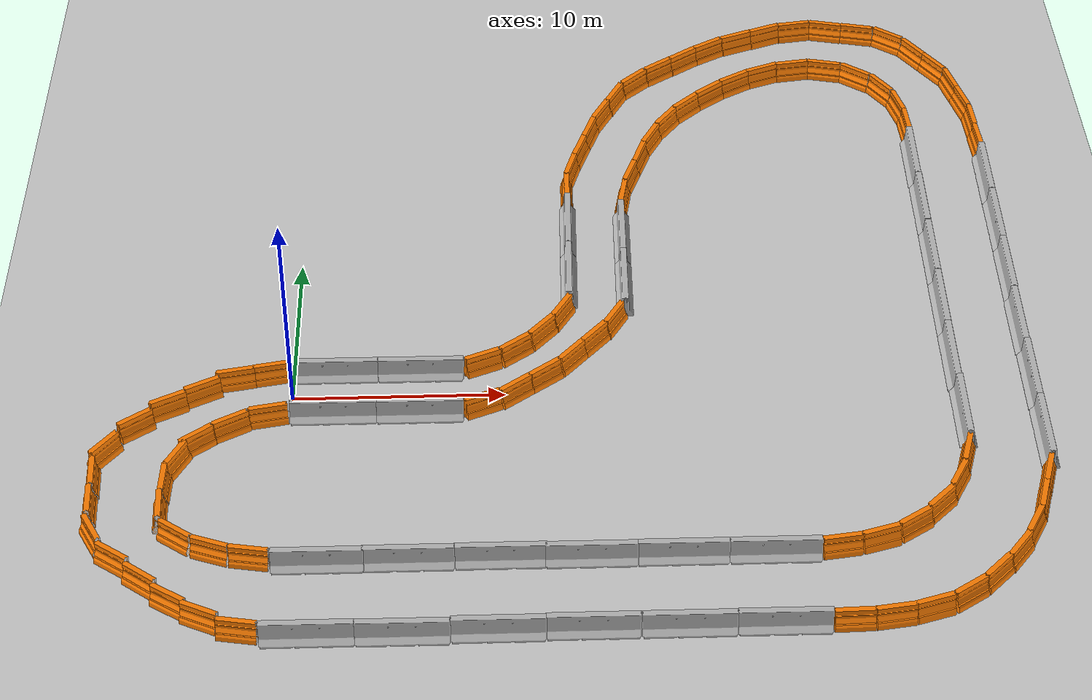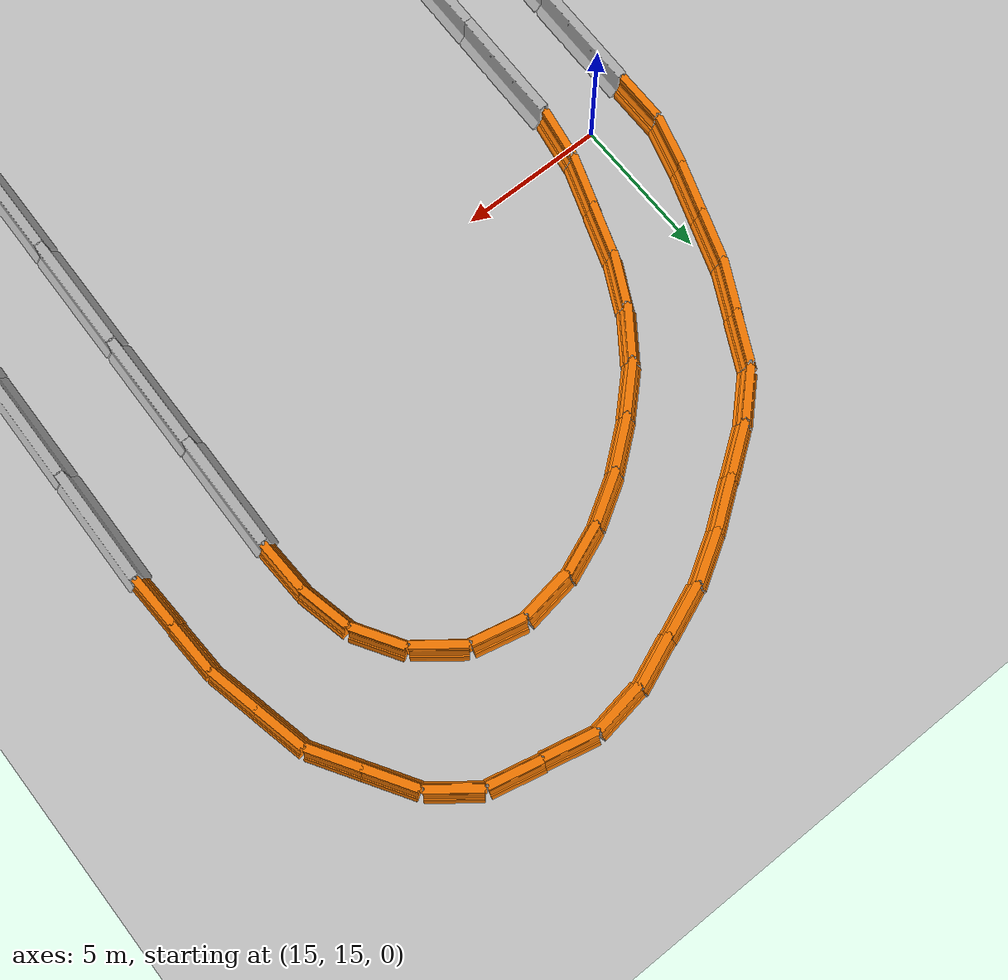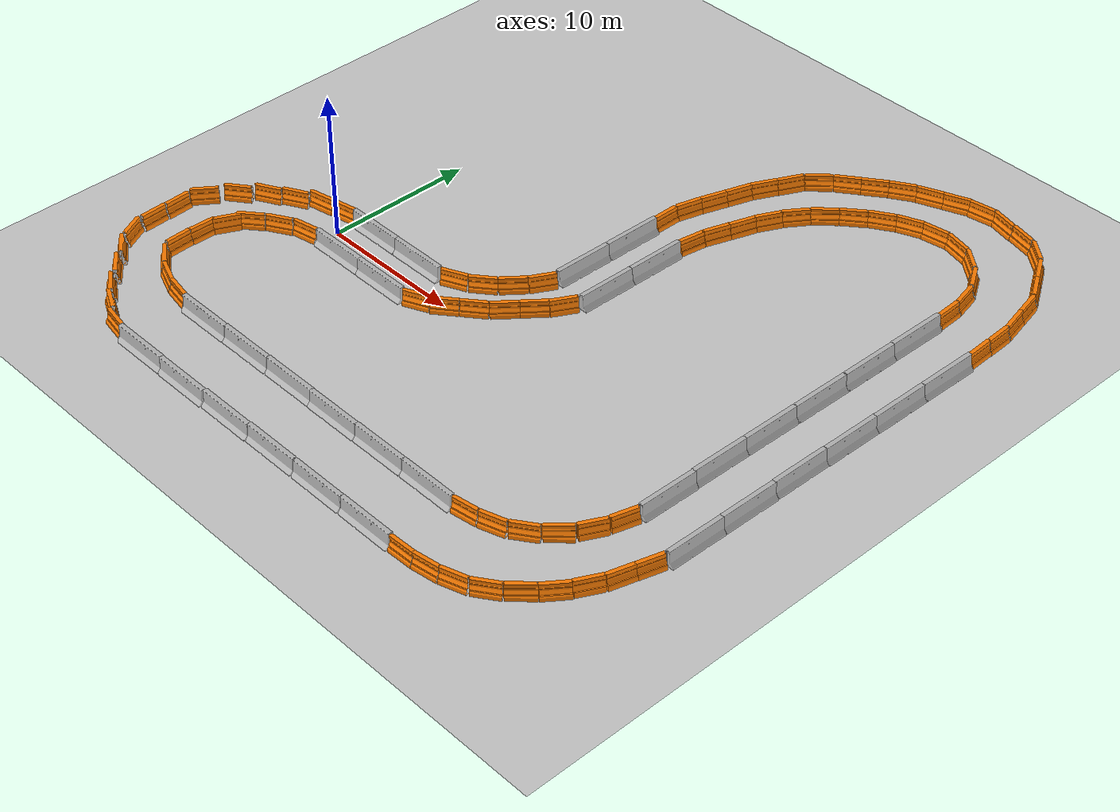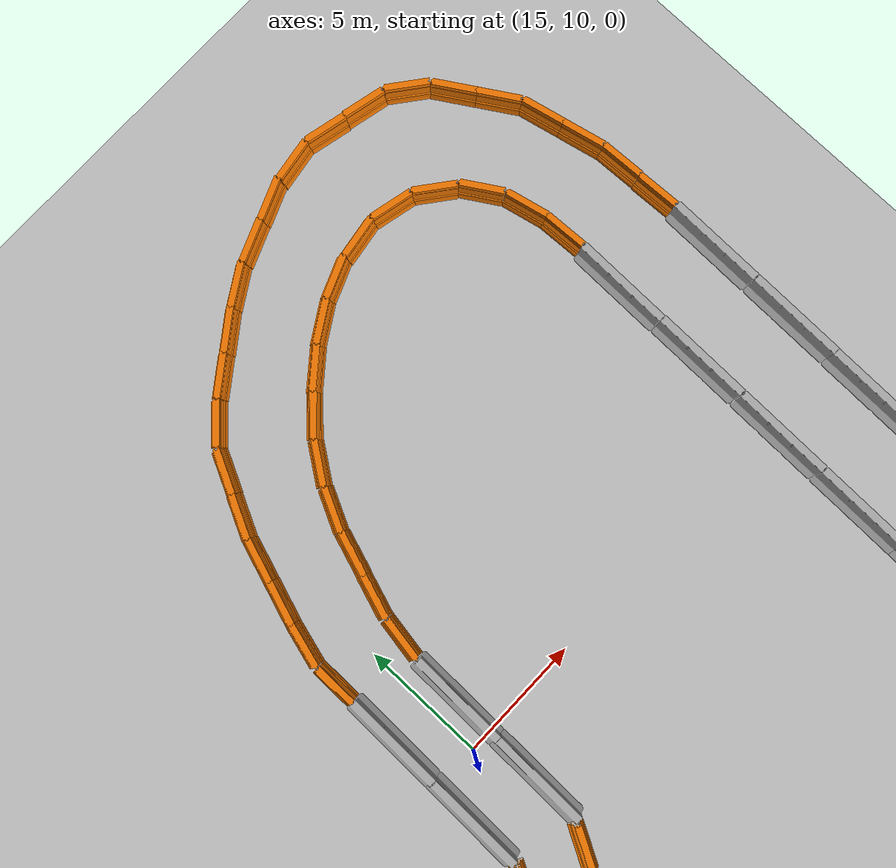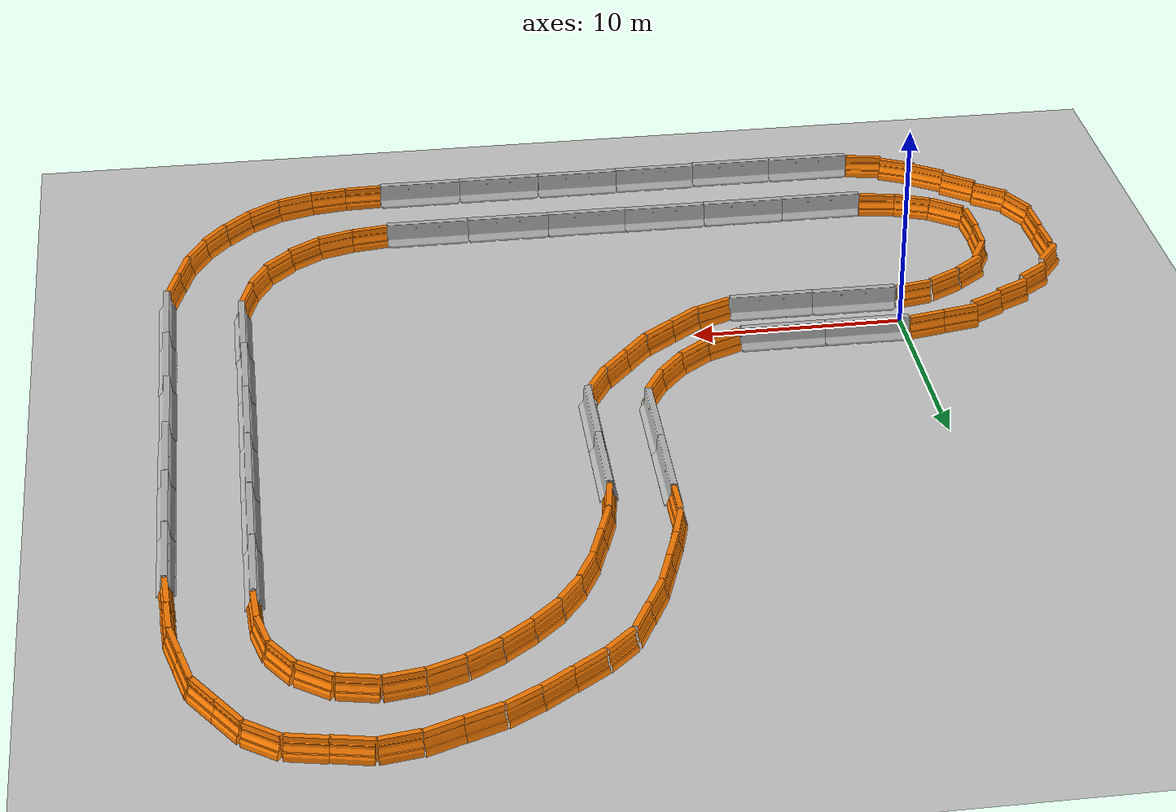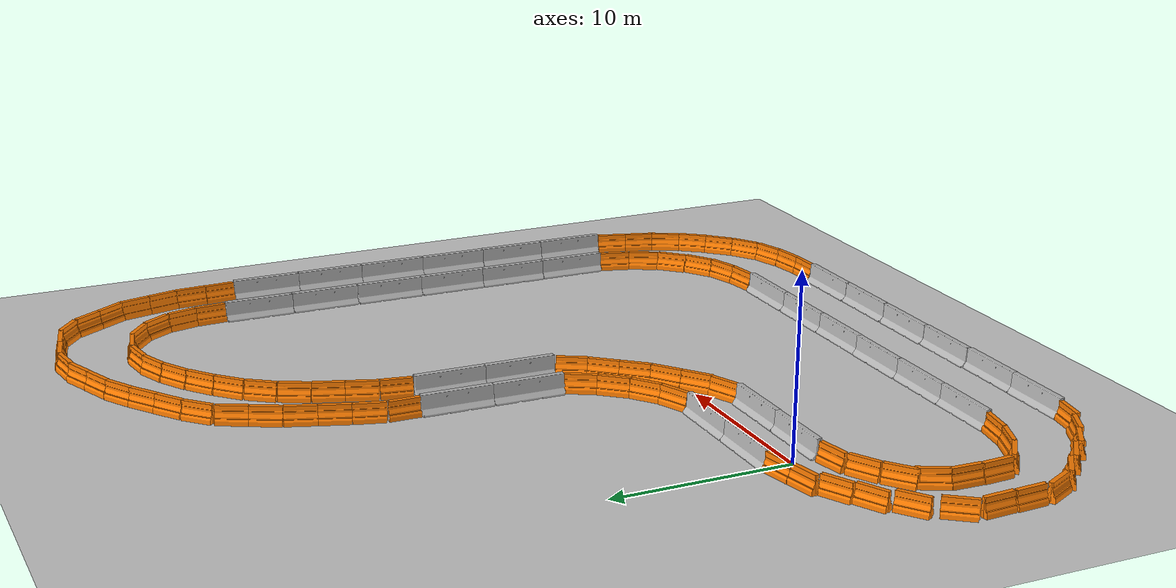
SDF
<sdf version="1.6">
 <world name="default">
  <light name="sun" type="directional">
   <pose>0 0 10 0 -0 0</pose>
   <diffuse>0.8 0.8 0.8 1</diffuse>
   <specular>0.1 0.1 0.1 1</specular>
   <attenuation>
    <range>1000</range>
    <constant>0.9</constant>
    <linear>0.01</linear>
    <quadratic>0.001</quadratic>
   </attenuation>
   <direction>-0.5 0.5 -1</direction>
  </light>
  <model name="ground_plane">
   <static>1</static>
   <link name="link">
    <collision name="collision">
     <geometry><plane><normal>0 0 1</normal><size>100 100</size></plane></geometry>
     <surface><friction><ode><mu>100</mu><mu2>50</mu2></ode></friction></surface>
    </collision>
    <visual name="visual">
     <cast_shadows>0</cast_shadows>
     <geometry><plane><normal>0 0 1</normal><size>100 100</size></plane></geometry>
     <material>
      <script><uri>file://media/materials/scripts/gazebo.material</uri><name>Gazebo/Grey</name></script>
     </material>
    </visual>
   </link>
  </model>
  <physics name="default_physics" default="0" type="ode">
   <max_step_size>0.01</max_step_size>
   <real_time_factor>1</real_time_factor>
   <real_time_update_rate>100</real_time_update_rate>
  </physics>
  <gravity>0 0 -9.8</gravity>
  <magnetic_field>6e-06 2.3e-05 -4.2e-05</magnetic_field>
  <atmosphere type="adiabatic"/>
  <scene><ambient>0.4 0.4 0.4 1</ambient><background>0.7 0.7 0.7 1</background><shadows>1</shadows></scene>
  <spherical_coordinates>
   <surface_model>EARTH_WGS84</surface_model>
   <latitude_deg>0</latitude_deg>
   <longitude_deg>0</longitude_deg>
   <elevation>0</elevation>
   <heading_deg>0</heading_deg>
  </spherical_coordinates>
  <model name="jersey_barrier_0">
   <static>1</static>
   <link name="link">
    <visual name="visual">
     <geometry>
      <mesh><uri>model://jersey_barrier/meshes/jersey_barrier.dae</uri><scale>1 1 1</scale></mesh>
     </geometry>
    </visual>
    <collision name="upright">
     <pose>0 0 0.5715 0 -0 0</pose>
     <geometry><box><size>4.06542 0.3063 1.143</size></box></geometry>
    </collision>
    <collision name="base">
     <pose>0 0 0.032258 0 -0 0</pose>
     <geometry><box><size>4.06542 0.8107 0.064516</size></box></geometry>
    </collision>
    <collision name="base2">
     <pose>0 0 0.1 0 -0 0</pose>
     <geometry><box><size>4.06542 0.65 0.1</size></box></geometry>
    </collision>
    <collision name="base3">
     <pose>0 0 0.2 0 -0 0</pose>
     <geometry><box><size>4.06542 0.5 0.1</size></box></geometry>
    </collision>
    <collision name="left-angle">
     <pose>0 -0.224 0.2401 0.9 -0 0</pose>
     <geometry><box><size>4.06542 0.5 0.064516</size></box></geometry>
    </collision>
    <collision name="right-angle">
     <pose>0 0.224 0.2401 -0.9 0 0</pose>
     <geometry><box><size>4.06542 0.5 0.064516</size></box></geometry>
    </collision>
   </link>
   <pose>1.97965 1.45207 0 0 -0 0</pose>
  </model>
  <model name="jersey_barrier_0_clone">
   <static>1</static>
   <link name="link">
    <visual name="visual">
     <geometry>
      <mesh><uri>model://jersey_barrier/meshes/jersey_barrier.dae</uri><scale>1 1 1</scale></mesh>
     </geometry>
    </visual>
    <collision name="upright">
     <pose>0 0 0.5715 0 -0 0</pose>
     <geometry><box><size>4.06542 0.3063 1.143</size></box></geometry>
    </collision>
    <collision name="base">
     <pose>0 0 0.032258 0 -0 0</pose>
     <geometry><box><size>4.06542 0.8107 0.064516</size></box></geometry>
    </collision>
    <collision name="base2">
     <pose>0 0 0.1 0 -0 0</pose>
     <geometry><box><size>4.06542 0.65 0.1</size></box></geometry>
    </collision>
    <collision name="base3">
     <pose>0 0 0.2 0 -0 0</pose>
     <geometry><box><size>4.06542 0.5 0.1</size></box></geometry>
    </collision>
    <collision name="left-angle">
     <pose>0 -0.224 0.2401 0.9 -0 0</pose>
     <geometry><box><size>4.06542 0.5 0.064516</size></box></geometry>
    </collision>
    <collision name="right-angle">
     <pose>0 0.224 0.2401 -0.9 0 0</pose>
     <geometry><box><size>4.06542 0.5 0.064516</size></box></geometry>
    </collision>
   </link>
   <pose>2.00755 -1.4776 0 0 -0 0</pose>
  </model>
  <model name="jersey_barrier_0_clone_0">
   <static>1</static>
   <link name="link">
    <visual name="visual">
     <geometry>
      <mesh><uri>model://jersey_barrier/meshes/jersey_barrier.dae</uri><scale>1 1 1</scale></mesh>
     </geometry>
    </visual>
    <collision name="upright">
     <pose>0 0 0.5715 0 -0 0</pose>
     <geometry><box><size>4.06542 0.3063 1.143</size></box></geometry>
    </collision>
    <collision name="base">
     <pose>0 0 0.032258 0 -0 0</pose>
     <geometry><box><size>4.06542 0.8107 0.064516</size></box></geometry>
    </collision>
    <collision name="base2">
     <pose>0 0 0.1 0 -0 0</pose>
     <geometry><box><size>4.06542 0.65 0.1</size></box></geometry>
    </collision>
    <collision name="base3">
     <pose>0 0 0.2 0 -0 0</pose>
     <geometry><box><size>4.06542 0.5 0.1</size></box></geometry>
    </collision>
    <collision name="left-angle">
     <pose>0 -0.224 0.2401 0.9 -0 0</pose>
     <geometry><box><size>4.06542 0.5 0.064516</size></box></geometry>
    </collision>
    <collision name="right-angle">
     <pose>0 0.224 0.2401 -0.9 0 0</pose>
     <geometry><box><size>4.06542 0.5 0.064516</size></box></geometry>
    </collision>
   </link>
   <pose>5.99858 1.44509 0 0 -0 0</pose>
  </model>
  <model name="jersey_barrier_0_clone_0_clone">
   <static>1</static>
   <link name="link">
    <visual name="visual">
     <geometry>
      <mesh><uri>model://jersey_barrier/meshes/jersey_barrier.dae</uri><scale>1 1 1</scale></mesh>
     </geometry>
    </visual>
    <collision name="upright">
     <pose>0 0 0.5715 0 -0 0</pose>
     <geometry><box><size>4.06542 0.3063 1.143</size></box></geometry>
    </collision>
    <collision name="base">
     <pose>0 0 0.032258 0 -0 0</pose>
     <geometry><box><size>4.06542 0.8107 0.064516</size></box></geometry>
    </collision>
    <collision name="base2">
     <pose>0 0 0.1 0 -0 0</pose>
     <geometry><box><size>4.06542 0.65 0.1</size></box></geometry>
    </collision>
    <collision name="base3">
     <pose>0 0 0.2 0 -0 0</pose>
     <geometry><box><size>4.06542 0.5 0.1</size></box></geometry>
    </collision>
    <collision name="left-angle">
     <pose>0 -0.224 0.2401 0.9 -0 0</pose>
     <geometry><box><size>4.06542 0.5 0.064516</size></box></geometry>
    </collision>
    <collision name="right-angle">
     <pose>0 0.224 0.2401 -0.9 0 0</pose>
     <geometry><box><size>4.06542 0.5 0.064516</size></box></geometry>
    </collision>
   </link>
   <pose>6.01454 -1.49668 0 0 -0 0</pose>
  </model>
  <model name="drc_practice_organge_jersey_barrier">
   <static>1</static>
   <link name="link">
    <visual name="visual">
     <geometry>
      <mesh>
       <uri>model://drc_practice_orange_jersey_barrier/meshes/jersey_barrier.dae</uri>
       <scale>1 1 1</scale>
      </mesh>
     </geometry>
    </visual>
    <collision name="collision">
     <geometry>
      <mesh>
       <uri>model://drc_practice_orange_jersey_barrier/meshes/jersey_barrier.dae</uri>
       <scale>1 1 1</scale>
      </mesh>
     </geometry>
    </collision>
   </link>
   <pose>8.94023 1.83416 0 0 0 -1.14589</pose>
  </model>
  <model name="drc_practice_organge_jersey_barrier_clone">
   <static>1</static>
   <link name="link">
    <visual name="visual">
     <geometry>
      <mesh>
       <uri>model://drc_practice_orange_jersey_barrier/meshes/jersey_barrier.dae</uri>
       <scale>1 1 1</scale>
      </mesh>
     </geometry>
    </visual>
    <collision name="collision">
     <geometry>
      <mesh>
       <uri>model://drc_practice_orange_jersey_barrier/meshes/jersey_barrier.dae</uri>
       <scale>1 1 1</scale>
      </mesh>
     </geometry>
    </collision>
   </link>
   <pose>8.92402 -1.13836 0 0 0 -1.14589</pose>
  </model>
  <model name="drc_practice_organge_jersey_barrier_clone_0">
   <static>1</static>
   <link name="link">
    <visual name="visual">
     <geometry>
      <mesh>
       <uri>model://drc_practice_orange_jersey_barrier/meshes/jersey_barrier.dae</uri>
       <scale>1 1 1</scale>
      </mesh>
     </geometry>
    </visual>
    <collision name="collision">
     <geometry>
      <mesh>
       <uri>model://drc_practice_orange_jersey_barrier/meshes/jersey_barrier.dae</uri>
       <scale>1 1 1</scale>
      </mesh>
     </geometry>
    </collision>
   </link>
   <pose>10.483 2.74563 0 0 0 -0.895836</pose>
  </model>
  <model name="drc_practice_organge_jersey_barrier_clone_0_clone">
   <static>1</static>
   <link name="link">
    <visual name="visual">
     <geometry>
      <mesh>
       <uri>model://drc_practice_orange_jersey_barrier/meshes/jersey_barrier.dae</uri>
       <scale>1 1 1</scale>
      </mesh>
     </geometry>
    </visual>
    <collision name="collision">
     <geometry>
      <mesh>
       <uri>model://drc_practice_orange_jersey_barrier/meshes/jersey_barrier.dae</uri>
       <scale>1 1 1</scale>
      </mesh>
     </geometry>
    </collision>
   </link>
   <pose>10.4581 -0.28408 0 0 0 -0.895836</pose>
  </model>
  <model name="drc_practice_organge_jersey_barrier_clone_0_clone_0">
   <static>1</static>
   <link name="link">
    <visual name="visual">
     <geometry>
      <mesh>
       <uri>model://drc_practice_orange_jersey_barrier/meshes/jersey_barrier.dae</uri>
       <scale>1 1 1</scale>
      </mesh>
     </geometry>
    </visual>
    <collision name="collision">
     <geometry>
      <mesh>
       <uri>model://drc_practice_orange_jersey_barrier/meshes/jersey_barrier.dae</uri>
       <scale>1 1 1</scale>
      </mesh>
     </geometry>
    </collision>
   </link>
   <pose>11.7617 4.00726 0 0 0 -0.68735</pose>
  </model>
  <model name="drc_practice_organge_jersey_barrier_clone_0_clone_clone">
   <static>1</static>
   <link name="link">
    <visual name="visual">
     <geometry>
      <mesh>
       <uri>model://drc_practice_orange_jersey_barrier/meshes/jersey_barrier.dae</uri>
       <scale>1 1 1</scale>
      </mesh>
     </geometry>
    </visual>
    <collision name="collision">
     <geometry>
      <mesh>
       <uri>model://drc_practice_orange_jersey_barrier/meshes/jersey_barrier.dae</uri>
       <scale>1 1 1</scale>
      </mesh>
     </geometry>
    </collision>
   </link>
   <pose>11.8548 0.818549 0 0 0 -0.895836</pose>
  </model>
  <model name="drc_practice_organge_jersey_barrier_clone_0_clone_0_clone">
   <static>1</static>
   <link name="link">
    <visual name="visual">
     <geometry>
      <mesh>
       <uri>model://drc_practice_orange_jersey_barrier/meshes/jersey_barrier.dae</uri>
       <scale>1 1 1</scale>
      </mesh>
     </geometry>
    </visual>
    <collision name="collision">
     <geometry>
      <mesh>
       <uri>model://drc_practice_orange_jersey_barrier/meshes/jersey_barrier.dae</uri>
       <scale>1 1 1</scale>
      </mesh>
     </geometry>
    </collision>
   </link>
   <pose>13.1462 2.06033 0 0 0 -0.68735</pose>
  </model>
  <model name="drc_practice_organge_jersey_barrier_clone_0_clone_0_clone_0">
   <static>1</static>
   <link name="link">
    <visual name="visual">
     <geometry>
      <mesh>
       <uri>model://drc_practice_orange_jersey_barrier/meshes/jersey_barrier.dae</uri>
       <scale>1 1 1</scale>
      </mesh>
     </geometry>
    </visual>
    <collision name="collision">
     <geometry>
      <mesh>
       <uri>model://drc_practice_orange_jersey_barrier/meshes/jersey_barrier.dae</uri>
       <scale>1 1 1</scale>
      </mesh>
     </geometry>
    </collision>
   </link>
   <pose>12.769 5.46834 0 0 0 -0.499455</pose>
  </model>
  <model name="drc_practice_organge_jersey_barrier_clone_0_clone_0_clone_clone">
   <static>1</static>
   <link name="link">
    <visual name="visual">
     <geometry>
      <mesh>
       <uri>model://drc_practice_orange_jersey_barrier/meshes/jersey_barrier.dae</uri>
       <scale>1 1 1</scale>
      </mesh>
     </geometry>
    </visual>
    <collision name="collision">
     <geometry>
      <mesh>
       <uri>model://drc_practice_orange_jersey_barrier/meshes/jersey_barrier.dae</uri>
       <scale>1 1 1</scale>
      </mesh>
     </geometry>
    </collision>
   </link>
   <pose>14.2642 3.41015 0 0 0 -0.68735</pose>
  </model>
  <model name="drc_practice_organge_jersey_barrier_clone_0_clone_0_clone_0_clone">
   <static>1</static>
   <link name="link">
    <visual name="visual">
     <geometry>
      <mesh>
       <uri>model://drc_practice_orange_jersey_barrier/meshes/jersey_barrier.dae</uri>
       <scale>1 1 1</scale>
      </mesh>
     </geometry>
    </visual>
    <collision name="collision">
     <geometry>
      <mesh>
       <uri>model://drc_practice_orange_jersey_barrier/meshes/jersey_barrier.dae</uri>
       <scale>1 1 1</scale>
      </mesh>
     </geometry>
    </collision>
   </link>
   <pose>15.2804 4.83523 0 0 0 -0.499455</pose>
  </model>
  <model name="jersey_barrier_1">
   <static>1</static>
   <link name="link">
    <visual name="visual">
     <geometry>
      <mesh><uri>model://jersey_barrier/meshes/jersey_barrier.dae</uri><scale>1 1 1</scale></mesh>
     </geometry>
    </visual>
    <collision name="upright">
     <pose>0 0 0.5715 0 -0 0</pose>
     <geometry><box><size>4.06542 0.3063 1.143</size></box></geometry>
    </collision>
    <collision name="base">
     <pose>0 0 0.032258 0 -0 0</pose>
     <geometry><box><size>4.06542 0.8107 0.064516</size></box></geometry>
    </collision>
    <collision name="base2">
     <pose>0 0 0.1 0 -0 0</pose>
     <geometry><box><size>4.06542 0.65 0.1</size></box></geometry>
    </collision>
    <collision name="base3">
     <pose>0 0 0.2 0 -0 0</pose>
     <geometry><box><size>4.06542 0.5 0.1</size></box></geometry>
    </collision>
    <collision name="left-angle">
     <pose>0 -0.224 0.2401 0.9 -0 0</pose>
     <geometry><box><size>4.06542 0.5 0.064516</size></box></geometry>
    </collision>
    <collision name="right-angle">
     <pose>0 0.224 0.2401 -0.9 0 0</pose>
     <geometry><box><size>4.06542 0.5 0.064516</size></box></geometry>
    </collision>
   </link>
   <pose>13.1944 8.34441 0 0 0 -1.5863</pose>
  </model>
  <model name="jersey_barrier_1_clone">
   <static>1</static>
   <link name="link">
    <visual name="visual">
     <geometry>
      <mesh><uri>model://jersey_barrier/meshes/jersey_barrier.dae</uri><scale>1 1 1</scale></mesh>
     </geometry>
    </visual>
    <collision name="upright">
     <pose>0 0 0.5715 0 -0 0</pose>
     <geometry><box><size>4.06542 0.3063 1.143</size></box></geometry>
    </collision>
    <collision name="base">
     <pose>0 0 0.032258 0 -0 0</pose>
     <geometry><box><size>4.06542 0.8107 0.064516</size></box></geometry>
    </collision>
    <collision name="base2">
     <pose>0 0 0.1 0 -0 0</pose>
     <geometry><box><size>4.06542 0.65 0.1</size></box></geometry>
    </collision>
    <collision name="base3">
     <pose>0 0 0.2 0 -0 0</pose>
     <geometry><box><size>4.06542 0.5 0.1</size></box></geometry>
    </collision>
    <collision name="left-angle">
     <pose>0 -0.224 0.2401 0.9 -0 0</pose>
     <geometry><box><size>4.06542 0.5 0.064516</size></box></geometry>
    </collision>
    <collision name="right-angle">
     <pose>0 0.224 0.2401 -0.9 0 0</pose>
     <geometry><box><size>4.06542 0.5 0.064516</size></box></geometry>
    </collision>
   </link>
   <pose>15.9038 7.70233 0 0 0 -1.5863</pose>
  </model>
  <model name="jersey_barrier_1_clone_0">
   <static>1</static>
   <link name="link">
    <visual name="visual">
     <geometry>
      <mesh><uri>model://jersey_barrier/meshes/jersey_barrier.dae</uri><scale>1 1 1</scale></mesh>
     </geometry>
    </visual>
    <collision name="upright">
     <pose>0 0 0.5715 0 -0 0</pose>
     <geometry><box><size>4.06542 0.3063 1.143</size></box></geometry>
    </collision>
    <collision name="base">
     <pose>0 0 0.032258 0 -0 0</pose>
     <geometry><box><size>4.06542 0.8107 0.064516</size></box></geometry>
    </collision>
    <collision name="base2">
     <pose>0 0 0.1 0 -0 0</pose>
     <geometry><box><size>4.06542 0.65 0.1</size></box></geometry>
    </collision>
    <collision name="base3">
     <pose>0 0 0.2 0 -0 0</pose>
     <geometry><box><size>4.06542 0.5 0.1</size></box></geometry>
    </collision>
    <collision name="left-angle">
     <pose>0 -0.224 0.2401 0.9 -0 0</pose>
     <geometry><box><size>4.06542 0.5 0.064516</size></box></geometry>
    </collision>
    <collision name="right-angle">
     <pose>0 0.224 0.2401 -0.9 0 0</pose>
     <geometry><box><size>4.06542 0.5 0.064516</size></box></geometry>
    </collision>
   </link>
   <pose>15.964 11.7226 0 0 0 -1.5863</pose>
  </model>
  <model name="jersey_barrier_1_clone_1">
   <static>1</static>
   <link name="link">
    <visual name="visual">
     <geometry>
      <mesh><uri>model://jersey_barrier/meshes/jersey_barrier.dae</uri><scale>1 1 1</scale></mesh>
     </geometry>
    </visual>
    <collision name="upright">
     <pose>0 0 0.5715 0 -0 0</pose>
     <geometry><box><size>4.06542 0.3063 1.143</size></box></geometry>
    </collision>
    <collision name="base">
     <pose>0 0 0.032258 0 -0 0</pose>
     <geometry><box><size>4.06542 0.8107 0.064516</size></box></geometry>
    </collision>
    <collision name="base2">
     <pose>0 0 0.1 0 -0 0</pose>
     <geometry><box><size>4.06542 0.65 0.1</size></box></geometry>
    </collision>
    <collision name="base3">
     <pose>0 0 0.2 0 -0 0</pose>
     <geometry><box><size>4.06542 0.5 0.1</size></box></geometry>
    </collision>
    <collision name="left-angle">
     <pose>0 -0.224 0.2401 0.9 -0 0</pose>
     <geometry><box><size>4.06542 0.5 0.064516</size></box></geometry>
    </collision>
    <collision name="right-angle">
     <pose>0 0.224 0.2401 -0.9 0 0</pose>
     <geometry><box><size>4.06542 0.5 0.064516</size></box></geometry>
    </collision>
   </link>
   <pose>13.2555 12.3903 0 0 0 -1.5863</pose>
  </model>
  <model name="drc_practice_organge_jersey_barrier_0">
   <static>1</static>
   <link name="link">
    <visual name="visual">
     <geometry>
      <mesh>
       <uri>model://drc_practice_orange_jersey_barrier/meshes/jersey_barrier.dae</uri>
       <scale>1 1 1</scale>
      </mesh>
     </geometry>
    </visual>
    <collision name="collision">
     <geometry>
      <mesh>
       <uri>model://drc_practice_orange_jersey_barrier/meshes/jersey_barrier.dae</uri>
       <scale>1 1 1</scale>
      </mesh>
     </geometry>
    </collision>
   </link>
   <pose>16.1418 14.7037 0 0 0 -0.159241</pose>
  </model>
  <model name="drc_practice_organge_jersey_barrier_1">
   <static>1</static>
   <link name="link">
    <visual name="visual">
     <geometry>
      <mesh>
       <uri>model://drc_practice_orange_jersey_barrier/meshes/jersey_barrier.dae</uri>
       <scale>1 1 1</scale>
      </mesh>
     </geometry>
    </visual>
    <collision name="collision">
     <geometry>
      <mesh>
       <uri>model://drc_practice_orange_jersey_barrier/meshes/jersey_barrier.dae</uri>
       <scale>1 1 1</scale>
      </mesh>
     </geometry>
    </collision>
   </link>
   <pose>13.2812 15.315 0 0 -0 0</pose>
  </model>
  <model name="drc_practice_organge_jersey_barrier_0_clone_0">
   <static>1</static>
   <link name="link">
    <visual name="visual">
     <geometry>
      <mesh>
       <uri>model://drc_practice_orange_jersey_barrier/meshes/jersey_barrier.dae</uri>
       <scale>1 1 1</scale>
      </mesh>
     </geometry>
    </visual>
    <collision name="collision">
     <geometry>
      <mesh>
       <uri>model://drc_practice_orange_jersey_barrier/meshes/jersey_barrier.dae</uri>
       <scale>1 1 1</scale>
      </mesh>
     </geometry>
    </collision>
   </link>
   <pose>16.5703 16.4699 0 0 0 -0.320373</pose>
  </model>
  <model name="drc_practice_organge_jersey_barrier_0_clone_0_clone">
   <static>1</static>
   <link name="link">
    <visual name="visual">
     <geometry>
      <mesh>
       <uri>model://drc_practice_orange_jersey_barrier/meshes/jersey_barrier.dae</uri>
       <scale>1 1 1</scale>
      </mesh>
     </geometry>
    </visual>
    <collision name="collision">
     <geometry>
      <mesh>
       <uri>model://drc_practice_orange_jersey_barrier/meshes/jersey_barrier.dae</uri>
       <scale>1 1 1</scale>
      </mesh>
     </geometry>
    </collision>
   </link>
   <pose>17.1479 18.1401 0 0 0 -0.320373</pose>
  </model>
  <model name="drc_practice_organge_jersey_barrier_0_clone_0_clone_0">
   <static>1</static>
   <link name="link">
    <visual name="visual">
     <geometry>
      <mesh>
       <uri>model://drc_practice_orange_jersey_barrier/meshes/jersey_barrier.dae</uri>
       <scale>1 1 1</scale>
      </mesh>
     </geometry>
    </visual>
    <collision name="collision">
     <geometry>
      <mesh>
       <uri>model://drc_practice_orange_jersey_barrier/meshes/jersey_barrier.dae</uri>
       <scale>1 1 1</scale>
      </mesh>
     </geometry>
    </collision>
   </link>
   <pose>13.5277 17.1222 0 0 0 -0.265206</pose>
  </model>
  <model name="drc_practice_organge_jersey_barrier_0_clone_0_clone_clone">
   <static>1</static>
   <link name="link">
    <visual name="visual">
     <geometry>
      <mesh>
       <uri>model://drc_practice_orange_jersey_barrier/meshes/jersey_barrier.dae</uri>
       <scale>1 1 1</scale>
      </mesh>
     </geometry>
    </visual>
    <collision name="collision">
     <geometry>
      <mesh>
       <uri>model://drc_practice_orange_jersey_barrier/meshes/jersey_barrier.dae</uri>
       <scale>1 1 1</scale>
      </mesh>
     </geometry>
    </collision>
   </link>
   <pose>14.0484 18.803 0 0 0 -0.320373</pose>
  </model>
  <model name="drc_practice_organge_jersey_barrier_0_clone_0_clone_clone_0">
   <static>1</static>
   <link name="link">
    <visual name="visual">
     <geometry>
      <mesh>
       <uri>model://drc_practice_orange_jersey_barrier/meshes/jersey_barrier.dae</uri>
       <scale>1 1 1</scale>
      </mesh>
     </geometry>
    </visual>
    <collision name="collision">
     <geometry>
      <mesh>
       <uri>model://drc_practice_orange_jersey_barrier/meshes/jersey_barrier.dae</uri>
       <scale>1 1 1</scale>
      </mesh>
     </geometry>
    </collision>
   </link>
   <pose>17.8079 19.7821 0 0 0 -0.458796</pose>
  </model>
  <model name="drc_practice_organge_jersey_barrier_0_clone_0_clone_clone_clone">
   <static>1</static>
   <link name="link">
    <visual name="visual">
     <geometry>
      <mesh>
       <uri>model://drc_practice_orange_jersey_barrier/meshes/jersey_barrier.dae</uri>
       <scale>1 1 1</scale>
      </mesh>
     </geometry>
    </visual>
    <collision name="collision">
     <geometry>
      <mesh>
       <uri>model://drc_practice_orange_jersey_barrier/meshes/jersey_barrier.dae</uri>
       <scale>1 1 1</scale>
      </mesh>
     </geometry>
    </collision>
   </link>
   <pose>14.6026 20.4536 0 0 0 -0.320373</pose>
  </model>
  <model name="drc_practice_organge_jersey_barrier_0_clone_0_clone_clone_0_clone">
   <static>1</static>
   <link name="link">
    <visual name="visual">
     <geometry>
      <mesh>
       <uri>model://drc_practice_orange_jersey_barrier/meshes/jersey_barrier.dae</uri>
       <scale>1 1 1</scale>
      </mesh>
     </geometry>
    </visual>
    <collision name="collision">
     <geometry>
      <mesh>
       <uri>model://drc_practice_orange_jersey_barrier/meshes/jersey_barrier.dae</uri>
       <scale>1 1 1</scale>
      </mesh>
     </geometry>
    </collision>
   </link>
   <pose>15.2701 22.0895 0 0 0 -0.458796</pose>
  </model>
  <model name="drc_practice_organge_jersey_barrier_0_clone_0_clone_clone_0_clone_0">
   <static>1</static>
   <link name="link">
    <visual name="visual">
     <geometry>
      <mesh>
       <uri>model://drc_practice_orange_jersey_barrier/meshes/jersey_barrier.dae</uri>
       <scale>1 1 1</scale>
      </mesh>
     </geometry>
    </visual>
    <collision name="collision">
     <geometry>
      <mesh>
       <uri>model://drc_practice_orange_jersey_barrier/meshes/jersey_barrier.dae</uri>
       <scale>1 1 1</scale>
      </mesh>
     </geometry>
    </collision>
   </link>
   <pose>18.7065 21.3447 0 0 0 -0.610482</pose>
  </model>
  <model name="drc_practice_organge_jersey_barrier_0_clone_0_clone_clone_0_clone_clone">
   <static>1</static>
   <link name="link">
    <visual name="visual">
     <geometry>
      <mesh>
       <uri>model://drc_practice_orange_jersey_barrier/meshes/jersey_barrier.dae</uri>
       <scale>1 1 1</scale>
      </mesh>
     </geometry>
    </visual>
    <collision name="collision">
     <geometry>
      <mesh>
       <uri>model://drc_practice_orange_jersey_barrier/meshes/jersey_barrier.dae</uri>
       <scale>1 1 1</scale>
      </mesh>
     </geometry>
    </collision>
   </link>
   <pose>16.0773 23.6599 0 0 0 -0.458796</pose>
  </model>
  <model name="drc_practice_organge_jersey_barrier_0_clone_0_clone_clone_0_clone_0_clone">
   <static>1</static>
   <link name="link">
    <visual name="visual">
     <geometry>
      <mesh>
       <uri>model://drc_practice_orange_jersey_barrier/meshes/jersey_barrier.dae</uri>
       <scale>1 1 1</scale>
      </mesh>
     </geometry>
    </visual>
    <collision name="collision">
     <geometry>
      <mesh>
       <uri>model://drc_practice_orange_jersey_barrier/meshes/jersey_barrier.dae</uri>
       <scale>1 1 1</scale>
      </mesh>
     </geometry>
    </collision>
   </link>
   <pose>19.8539 22.7324 0 0 0 -0.790237</pose>
  </model>
  <model name="drc_practice_organge_jersey_barrier_0_clone_0_clone_clone_0_clone_0_clone_clone">
   <static>1</static>
   <link name="link">
    <visual name="visual">
     <geometry>
      <mesh>
       <uri>model://drc_practice_orange_jersey_barrier/meshes/jersey_barrier.dae</uri>
       <scale>1 1 1</scale>
      </mesh>
     </geometry>
    </visual>
    <collision name="collision">
     <geometry>
      <mesh>
       <uri>model://drc_practice_orange_jersey_barrier/meshes/jersey_barrier.dae</uri>
       <scale>1 1 1</scale>
      </mesh>
     </geometry>
    </collision>
   </link>
   <pose>17.1714 25.144 0 0 0 -0.790237</pose>
  </model>
  <model name="drc_practice_organge_jersey_barrier_0_clone_0_clone_clone_0_clone_0_clone_clone_clone">
   <static>1</static>
   <link name="link">
    <visual name="visual">
     <geometry>
      <mesh>
       <uri>model://drc_practice_orange_jersey_barrier/meshes/jersey_barrier.dae</uri>
       <scale>1 1 1</scale>
      </mesh>
     </geometry>
    </visual>
    <collision name="collision">
     <geometry>
      <mesh>
       <uri>model://drc_practice_orange_jersey_barrier/meshes/jersey_barrier.dae</uri>
       <scale>1 1 1</scale>
      </mesh>
     </geometry>
    </collision>
   </link>
   <pose>18.5639 26.3044 0 0 0 -0.933401</pose>
  </model>
  <model name="drc_practice_organge_jersey_barrier_0_clone_0_clone_clone_0_clone_0_clone_clone_0">
   <static>1</static>
   <link name="link">
    <visual name="visual">
     <geometry>
      <mesh>
       <uri>model://drc_practice_orange_jersey_barrier/meshes/jersey_barrier.dae</uri>
       <scale>1 1 1</scale>
      </mesh>
     </geometry>
    </visual>
    <collision name="collision">
     <geometry>
      <mesh>
       <uri>model://drc_practice_orange_jersey_barrier/meshes/jersey_barrier.dae</uri>
       <scale>1 1 1</scale>
      </mesh>
     </geometry>
    </collision>
   </link>
   <pose>21.1732 23.9264 0 0 0 -0.888354</pose>
  </model>
  <model name="drc_practice_organge_jersey_barrier_0_clone_0_clone_clone_0_clone_0_clone_clone_clone_clone">
   <static>1</static>
   <link name="link">
    <visual name="visual">
     <geometry>
      <mesh>
       <uri>model://drc_practice_orange_jersey_barrier/meshes/jersey_barrier.dae</uri>
       <scale>1 1 1</scale>
      </mesh>
     </geometry>
    </visual>
    <collision name="collision">
     <geometry>
      <mesh>
       <uri>model://drc_practice_orange_jersey_barrier/meshes/jersey_barrier.dae</uri>
       <scale>1 1 1</scale>
      </mesh>
     </geometry>
    </collision>
   </link>
   <pose>19.9619 27.3083 0 0 0 -0.933401</pose>
  </model>
  <model name="drc_practice_organge_jersey_barrier_0_clone_0_clone_clone_0_clone_0_clone_clone_0_clone">
   <static>1</static>
   <link name="link">
    <visual name="visual">
     <geometry>
      <mesh>
       <uri>model://drc_practice_orange_jersey_barrier/meshes/jersey_barrier.dae</uri>
       <scale>1 1 1</scale>
      </mesh>
     </geometry>
    </visual>
    <collision name="collision">
     <geometry>
      <mesh>
       <uri>model://drc_practice_orange_jersey_barrier/meshes/jersey_barrier.dae</uri>
       <scale>1 1 1</scale>
      </mesh>
     </geometry>
    </collision>
   </link>
   <pose>22.6179 24.9707 0 0 0 -1.01538</pose>
  </model>
  <model name="drc_practice_organge_jersey_barrier_0_clone_0_clone_clone_0_clone_0_clone_clone_0_clone_clone">
   <static>1</static>
   <link name="link">
    <visual name="visual">
     <geometry>
      <mesh>
       <uri>model://drc_practice_orange_jersey_barrier/meshes/jersey_barrier.dae</uri>
       <scale>1 1 1</scale>
      </mesh>
     </geometry>
    </visual>
    <collision name="collision">
     <geometry>
      <mesh>
       <uri>model://drc_practice_orange_jersey_barrier/meshes/jersey_barrier.dae</uri>
       <scale>1 1 1</scale>
      </mesh>
     </geometry>
    </collision>
   </link>
   <pose>21.4219 28.2774 0 0 0 -1.01538</pose>
  </model>
  <model name="drc_practice_organge_jersey_barrier_0_clone_0_clone_clone_0_clone_0_clone_clone_0_clone_clone_0">
   <static>1</static>
   <link name="link">
    <visual name="visual">
     <geometry>
      <mesh>
       <uri>model://drc_practice_orange_jersey_barrier/meshes/jersey_barrier.dae</uri>
       <scale>1 1 1</scale>
      </mesh>
     </geometry>
    </visual>
    <collision name="collision">
     <geometry>
      <mesh>
       <uri>model://drc_practice_orange_jersey_barrier/meshes/jersey_barrier.dae</uri>
       <scale>1 1 1</scale>
      </mesh>
     </geometry>
    </collision>
   </link>
   <pose>24.2054 25.7784 0 0 0 -1.18059</pose>
  </model>
  <model name="drc_practice_organge_jersey_barrier_0_clone_0_clone_clone_0_clone_0_clone_clone_0_clone_clone_0_clone">
   <static>1</static>
   <link name="link">
    <visual name="visual">
     <geometry>
      <mesh>
       <uri>model://drc_practice_orange_jersey_barrier/meshes/jersey_barrier.dae</uri>
       <scale>1 1 1</scale>
      </mesh>
     </geometry>
    </visual>
    <collision name="collision">
     <geometry>
      <mesh>
       <uri>model://drc_practice_orange_jersey_barrier/meshes/jersey_barrier.dae</uri>
       <scale>1 1 1</scale>
      </mesh>
     </geometry>
    </collision>
   </link>
   <pose>23.0379 29.0549 0 0 0 -1.18059</pose>
  </model>
  <model name="drc_practice_organge_jersey_barrier_0_clone_0_clone_clone_0_clone_0_clone_clone_0_clone_clone_0_clone_0">
   <static>1</static>
   <link name="link">
    <visual name="visual">
     <geometry>
      <mesh>
       <uri>model://drc_practice_orange_jersey_barrier/meshes/jersey_barrier.dae</uri>
       <scale>1 1 1</scale>
      </mesh>
     </geometry>
    </visual>
    <collision name="collision">
     <geometry>
      <mesh>
       <uri>model://drc_practice_orange_jersey_barrier/meshes/jersey_barrier.dae</uri>
       <scale>1 1 1</scale>
      </mesh>
     </geometry>
    </collision>
   </link>
   <pose>24.6692 29.6916 0 0 0 -1.18059</pose>
  </model>
  <model name="drc_practice_organge_jersey_barrier_0_clone_0_clone_clone_0_clone_0_clone_clone_0_clone_clone_0_clone_1">
   <static>1</static>
   <link name="link">
    <visual name="visual">
     <geometry>
      <mesh>
       <uri>model://drc_practice_orange_jersey_barrier/meshes/jersey_barrier.dae</uri>
       <scale>1 1 1</scale>
      </mesh>
     </geometry>
    </visual>
    <collision name="collision">
     <geometry>
      <mesh>
       <uri>model://drc_practice_orange_jersey_barrier/meshes/jersey_barrier.dae</uri>
       <scale>1 1 1</scale>
      </mesh>
     </geometry>
    </collision>
   </link>
   <pose>25.8939 26.2054 0 0 0 -1.4084</pose>
  </model>
  <model name="drc_practice_organge_jersey_barrier_0_clone_0_clone_clone_0_clone_0_clone_clone_0_clone_clone_0_clone_1_clone">
   <static>1</static>
   <link name="link">
    <visual name="visual">
     <geometry>
      <mesh>
       <uri>model://drc_practice_orange_jersey_barrier/meshes/jersey_barrier.dae</uri>
       <scale>1 1 1</scale>
      </mesh>
     </geometry>
    </visual>
    <collision name="collision">
     <geometry>
      <mesh>
       <uri>model://drc_practice_orange_jersey_barrier/meshes/jersey_barrier.dae</uri>
       <scale>1 1 1</scale>
      </mesh>
     </geometry>
    </collision>
   </link>
   <pose>26.3514 30.1012 0 0 0 -1.4084</pose>
  </model>
  <model name="drc_practice_organge_jersey_barrier_0_clone_0_clone_clone_0_clone_0_clone_clone_0_clone_clone_0_clone_1_clone_0">
   <static>1</static>
   <link name="link">
    <visual name="visual">
     <geometry>
      <mesh>
       <uri>model://drc_practice_orange_jersey_barrier/meshes/jersey_barrier.dae</uri>
       <scale>1 1 1</scale>
      </mesh>
     </geometry>
    </visual>
    <collision name="collision">
     <geometry>
      <mesh>
       <uri>model://drc_practice_orange_jersey_barrier/meshes/jersey_barrier.dae</uri>
       <scale>1 1 1</scale>
      </mesh>
     </geometry>
    </collision>
   </link>
   <pose>27.675 26.1449 0 0 0 -1.79124</pose>
  </model>
  <model name="drc_practice_organge_jersey_barrier_0_clone_0_clone_clone_0_clone_0_clone_clone_0_clone_clone_0_clone_1_clone_0_clone">
   <static>1</static>
   <link name="link">
    <visual name="visual">
     <geometry>
      <mesh>
       <uri>model://drc_practice_orange_jersey_barrier/meshes/jersey_barrier.dae</uri>
       <scale>1 1 1</scale>
      </mesh>
     </geometry>
    </visual>
    <collision name="collision">
     <geometry>
      <mesh>
       <uri>model://drc_practice_orange_jersey_barrier/meshes/jersey_barrier.dae</uri>
       <scale>1 1 1</scale>
      </mesh>
     </geometry>
    </collision>
   </link>
   <pose>28.1326 30.0439 0 0 0 -1.79124</pose>
  </model>
  <model name="drc_practice_organge_jersey_barrier_0_clone_0_clone_clone_0_clone_0_clone_clone_0_clone_clone_0_clone_1_clone_0_clone_0">
   <static>1</static>
   <link name="link">
    <visual name="visual">
     <geometry>
      <mesh>
       <uri>model://drc_practice_orange_jersey_barrier/meshes/jersey_barrier.dae</uri>
       <scale>1 1 1</scale>
      </mesh>
     </geometry>
    </visual>
    <collision name="collision">
     <geometry>
      <mesh>
       <uri>model://drc_practice_orange_jersey_barrier/meshes/jersey_barrier.dae</uri>
       <scale>1 1 1</scale>
      </mesh>
     </geometry>
    </collision>
   </link>
   <pose>29.3003 25.4079 0 0 0 -2.22537</pose>
  </model>
  <model name="drc_practice_organge_jersey_barrier_0_clone_0_clone_clone_0_clone_0_clone_clone_0_clone_clone_0_clone_1_clone_0_clone_clone">
   <static>1</static>
   <link name="link">
    <visual name="visual">
     <geometry>
      <mesh>
       <uri>model://drc_practice_orange_jersey_barrier/meshes/jersey_barrier.dae</uri>
       <scale>1 1 1</scale>
      </mesh>
     </geometry>
    </visual>
    <collision name="collision">
     <geometry>
      <mesh>
       <uri>model://drc_practice_orange_jersey_barrier/meshes/jersey_barrier.dae</uri>
       <scale>1 1 1</scale>
      </mesh>
     </geometry>
    </collision>
   </link>
   <pose>29.8571 29.6882 0 0 0 -1.79124</pose>
  </model>
  <model name="drc_practice_organge_jersey_barrier_0_clone_0_clone_clone_0_clone_0_clone_clone_0_clone_clone_0_clone_1_clone_0_clone_0_clone">
   <static>1</static>
   <link name="link">
    <visual name="visual">
     <geometry>
      <mesh>
       <uri>model://drc_practice_orange_jersey_barrier/meshes/jersey_barrier.dae</uri>
       <scale>1 1 1</scale>
      </mesh>
     </geometry>
    </visual>
    <collision name="collision">
     <geometry>
      <mesh>
       <uri>model://drc_practice_orange_jersey_barrier/meshes/jersey_barrier.dae</uri>
       <scale>1 1 1</scale>
      </mesh>
     </geometry>
    </collision>
   </link>
   <pose>31.5089 28.9517 0 0 0 -2.22537</pose>
  </model>
  <model name="drc_practice_organge_jersey_barrier_0_clone_0_clone_clone_0_clone_0_clone_clone_0_clone_clone_0_clone_1_clone_0_clone_0_clone_0">
   <static>1</static>
   <link name="link">
    <visual name="visual">
     <geometry>
      <mesh>
       <uri>model://drc_practice_orange_jersey_barrier/meshes/jersey_barrier.dae</uri>
       <scale>1 1 1</scale>
      </mesh>
     </geometry>
    </visual>
    <collision name="collision">
     <geometry>
      <mesh>
       <uri>model://drc_practice_orange_jersey_barrier/meshes/jersey_barrier.dae</uri>
       <scale>1 1 1</scale>
      </mesh>
     </geometry>
    </collision>
   </link>
   <pose>30.5447 24.1025 0 0 0 -2.57791</pose>
  </model>
  <model name="drc_practice_organge_jersey_barrier_0_clone_0_clone_clone_0_clone_0_clone_clone_0_clone_clone_0_clone_1_clone_0_clone_0_clone_0_clone">
   <static>1</static>
   <link name="link">
    <visual name="visual">
     <geometry>
      <mesh>
       <uri>model://drc_practice_orange_jersey_barrier/meshes/jersey_barrier.dae</uri>
       <scale>1 1 1</scale>
      </mesh>
     </geometry>
    </visual>
    <collision name="collision">
     <geometry>
      <mesh>
       <uri>model://drc_practice_orange_jersey_barrier/meshes/jersey_barrier.dae</uri>
       <scale>1 1 1</scale>
      </mesh>
     </geometry>
    </collision>
   </link>
   <pose>32.7275 27.5833 0 0 0 -2.57791</pose>
  </model>
  <model name="drc_practice_organge_jersey_barrier_0_clone_0_clone_clone_0_clone_0_clone_clone_0_clone_clone_0_clone_1_clone_0_clone_0_clone_0_clone_0">
   <static>1</static>
   <link name="link">
    <visual name="visual">
     <geometry>
      <mesh>
       <uri>model://drc_practice_orange_jersey_barrier/meshes/jersey_barrier.dae</uri>
       <scale>1 1 1</scale>
      </mesh>
     </geometry>
    </visual>
    <collision name="collision">
     <geometry>
      <mesh>
       <uri>model://drc_practice_orange_jersey_barrier/meshes/jersey_barrier.dae</uri>
       <scale>1 1 1</scale>
      </mesh>
     </geometry>
    </collision>
   </link>
   <pose>33.6532 26.1056 0 0 0 -2.57791</pose>
  </model>
  <model name="drc_practice_organge_jersey_barrier_0_clone_0_clone_clone_0_clone_0_clone_clone_0_clone_clone_0_clone_1_clone_0_clone_0_clone_0_clone_1">
   <static>1</static>
   <link name="link">
    <visual name="visual">
     <geometry>
      <mesh>
       <uri>model://drc_practice_orange_jersey_barrier/meshes/jersey_barrier.dae</uri>
       <scale>1 1 1</scale>
      </mesh>
     </geometry>
    </visual>
    <collision name="collision">
     <geometry>
      <mesh>
       <uri>model://drc_practice_orange_jersey_barrier/meshes/jersey_barrier.dae</uri>
       <scale>1 1 1</scale>
      </mesh>
     </geometry>
    </collision>
   </link>
   <pose>31.2455 22.4094 0 0 0 -2.91197</pose>
  </model>
  <model name="drc_practice_organge_jersey_barrier_0_clone_0_clone_clone_0_clone_0_clone_clone_0_clone_clone_0_clone_1_clone_0_clone_0_clone_0_clone_1_clone">
   <static>1</static>
   <link name="link">
    <visual name="visual">
     <geometry>
      <mesh>
       <uri>model://drc_practice_orange_jersey_barrier/meshes/jersey_barrier.dae</uri>
       <scale>1 1 1</scale>
      </mesh>
     </geometry>
    </visual>
    <collision name="collision">
     <geometry>
      <mesh>
       <uri>model://drc_practice_orange_jersey_barrier/meshes/jersey_barrier.dae</uri>
       <scale>1 1 1</scale>
      </mesh>
     </geometry>
    </collision>
   </link>
   <pose>34.3558 24.445 0 0 0 -2.91197</pose>
  </model>
  <model name="drc_practice_organge_jersey_barrier_0_clone_0_clone_clone_0_clone_0_clone_clone_0_clone_clone_0_clone_1_clone_0_clone_0_clone_0_clone_1_clone_0">
   <static>1</static>
   <link name="link">
    <visual name="visual">
     <geometry>
      <mesh>
       <uri>model://drc_practice_orange_jersey_barrier/meshes/jersey_barrier.dae</uri>
       <scale>1 1 1</scale>
      </mesh>
     </geometry>
    </visual>
    <collision name="collision">
     <geometry>
      <mesh>
       <uri>model://drc_practice_orange_jersey_barrier/meshes/jersey_barrier.dae</uri>
       <scale>1 1 1</scale>
      </mesh>
     </geometry>
    </collision>
   </link>
   <pose>34.7441 22.7273 0 0 0 -2.91197</pose>
  </model>
  <model name="drc_practice_organge_jersey_barrier_0_clone_0_clone_clone_0_clone_0_clone_clone_0_clone_clone_0_clone_1_clone_0_clone_0_clone_0_clone_1_clone_1">
   <static>1</static>
   <link name="link">
    <visual name="visual">
     <geometry>
      <mesh>
       <uri>model://drc_practice_orange_jersey_barrier/meshes/jersey_barrier.dae</uri>
       <scale>1 1 1</scale>
      </mesh>
     </geometry>
    </visual>
    <collision name="collision">
     <geometry>
      <mesh>
       <uri>model://drc_practice_orange_jersey_barrier/meshes/jersey_barrier.dae</uri>
       <scale>1 1 1</scale>
      </mesh>
     </geometry>
    </collision>
   </link>
   <pose>31.4766 20.6579 0 0 0 -3.09173</pose>
  </model>
  <model name="drc_practice_organge_jersey_barrier_0_clone_0_clone_clone_0_clone_0_clone_clone_0_clone_clone_0_clone_1_clone_0_clone_0_clone_0_clone_1_clone_1_clone">
   <static>1</static>
   <link name="link">
    <visual name="visual">
     <geometry>
      <mesh>
       <uri>model://drc_practice_orange_jersey_barrier/meshes/jersey_barrier.dae</uri>
       <scale>1 1 1</scale>
      </mesh>
     </geometry>
    </visual>
    <collision name="collision">
     <geometry>
      <mesh>
       <uri>model://drc_practice_orange_jersey_barrier/meshes/jersey_barrier.dae</uri>
       <scale>1 1 1</scale>
      </mesh>
     </geometry>
    </collision>
   </link>
   <pose>34.9886 20.9434 0 0 0 -3.09173</pose>
  </model>
  <model name="drc_practice_organge_jersey_barrier_0_clone_0_clone_clone_0_clone_0_clone_clone_0_clone_clone_0_clone_1_clone_0_clone_0_clone_0_clone_1_clone_1_clone_0">
   <static>1</static>
   <link name="link">
    <visual name="visual">
     <geometry>
      <mesh>
       <uri>model://drc_practice_orange_jersey_barrier/meshes/jersey_barrier.dae</uri>
       <scale>1 1 1</scale>
      </mesh>
     </geometry>
    </visual>
    <collision name="collision">
     <geometry>
      <mesh>
       <uri>model://drc_practice_orange_jersey_barrier/meshes/jersey_barrier.dae</uri>
       <scale>1 1 1</scale>
      </mesh>
     </geometry>
    </collision>
   </link>
   <pose>35.0409 19.161 0 0 0 -3.09173</pose>
  </model>
  <model name="jersey_barrier_1_clone_clone">
   <static>1</static>
   <link name="link">
    <visual name="visual">
     <geometry>
      <mesh><uri>model://jersey_barrier/meshes/jersey_barrier.dae</uri><scale>1 1 1</scale></mesh>
     </geometry>
    </visual>
    <collision name="upright">
     <pose>0 0 0.5715 0 -0 0</pose>
     <geometry><box><size>4.06542 0.3063 1.143</size></box></geometry>
    </collision>
    <collision name="base">
     <pose>0 0 0.032258 0 -0 0</pose>
     <geometry><box><size>4.06542 0.8107 0.064516</size></box></geometry>
    </collision>
    <collision name="base2">
     <pose>0 0 0.1 0 -0 0</pose>
     <geometry><box><size>4.06542 0.65 0.1</size></box></geometry>
    </collision>
    <collision name="base3">
     <pose>0 0 0.2 0 -0 0</pose>
     <geometry><box><size>4.06542 0.5 0.1</size></box></geometry>
    </collision>
    <collision name="left-angle">
     <pose>0 -0.224 0.2401 0.9 -0 0</pose>
     <geometry><box><size>4.06542 0.5 0.064516</size></box></geometry>
    </collision>
    <collision name="right-angle">
     <pose>0 0.224 0.2401 -0.9 0 0</pose>
     <geometry><box><size>4.06542 0.5 0.064516</size></box></geometry>
    </collision>
   </link>
   <pose>31.456 17.738 0 0 0 -1.5863</pose>
  </model>
  <model name="jersey_barrier_1_clone_clone_0">
   <static>1</static>
   <link name="link">
    <visual name="visual">
     <geometry>
      <mesh><uri>model://jersey_barrier/meshes/jersey_barrier.dae</uri><scale>1 1 1</scale></mesh>
     </geometry>
    </visual>
    <collision name="upright">
     <pose>0 0 0.5715 0 -0 0</pose>
     <geometry><box><size>4.06542 0.3063 1.143</size></box></geometry>
    </collision>
    <collision name="base">
     <pose>0 0 0.032258 0 -0 0</pose>
     <geometry><box><size>4.06542 0.8107 0.064516</size></box></geometry>
    </collision>
    <collision name="base2">
     <pose>0 0 0.1 0 -0 0</pose>
     <geometry><box><size>4.06542 0.65 0.1</size></box></geometry>
    </collision>
    <collision name="base3">
     <pose>0 0 0.2 0 -0 0</pose>
     <geometry><box><size>4.06542 0.5 0.1</size></box></geometry>
    </collision>
    <collision name="left-angle">
     <pose>0 -0.224 0.2401 0.9 -0 0</pose>
     <geometry><box><size>4.06542 0.5 0.064516</size></box></geometry>
    </collision>
    <collision name="right-angle">
     <pose>0 0.224 0.2401 -0.9 0 0</pose>
     <geometry><box><size>4.06542 0.5 0.064516</size></box></geometry>
    </collision>
   </link>
   <pose>35.0573 16.2417 0 0 0 -1.5863</pose>
  </model>
  <model name="jersey_barrier_1_clone_clone_clone">
   <static>1</static>
   <link name="link">
    <visual name="visual">
     <geometry>
      <mesh><uri>model://jersey_barrier/meshes/jersey_barrier.dae</uri><scale>1 1 1</scale></mesh>
     </geometry>
    </visual>
    <collision name="upright">
     <pose>0 0 0.5715 0 -0 0</pose>
     <geometry><box><size>4.06542 0.3063 1.143</size></box></geometry>
    </collision>
    <collision name="base">
     <pose>0 0 0.032258 0 -0 0</pose>
     <geometry><box><size>4.06542 0.8107 0.064516</size></box></geometry>
    </collision>
    <collision name="base2">
     <pose>0 0 0.1 0 -0 0</pose>
     <geometry><box><size>4.06542 0.65 0.1</size></box></geometry>
    </collision>
    <collision name="base3">
     <pose>0 0 0.2 0 -0 0</pose>
     <geometry><box><size>4.06542 0.5 0.1</size></box></geometry>
    </collision>
    <collision name="left-angle">
     <pose>0 -0.224 0.2401 0.9 -0 0</pose>
     <geometry><box><size>4.06542 0.5 0.064516</size></box></geometry>
    </collision>
    <collision name="right-angle">
     <pose>0 0.224 0.2401 -0.9 0 0</pose>
     <geometry><box><size>4.06542 0.5 0.064516</size></box></geometry>
    </collision>
   </link>
   <pose>31.4173 13.7035 0 0 0 -1.5863</pose>
  </model>
  <model name="jersey_barrier_1_clone_clone_clone_0">
   <static>1</static>
   <link name="link">
    <visual name="visual">
     <geometry>
      <mesh><uri>model://jersey_barrier/meshes/jersey_barrier.dae</uri><scale>1 1 1</scale></mesh>
     </geometry>
    </visual>
    <collision name="upright">
     <pose>0 0 0.5715 0 -0 0</pose>
     <geometry><box><size>4.06542 0.3063 1.143</size></box></geometry>
    </collision>
    <collision name="base">
     <pose>0 0 0.032258 0 -0 0</pose>
     <geometry><box><size>4.06542 0.8107 0.064516</size></box></geometry>
    </collision>
    <collision name="base2">
     <pose>0 0 0.1 0 -0 0</pose>
     <geometry><box><size>4.06542 0.65 0.1</size></box></geometry>
    </collision>
    <collision name="base3">
     <pose>0 0 0.2 0 -0 0</pose>
     <geometry><box><size>4.06542 0.5 0.1</size></box></geometry>
    </collision>
    <collision name="left-angle">
     <pose>0 -0.224 0.2401 0.9 -0 0</pose>
     <geometry><box><size>4.06542 0.5 0.064516</size></box></geometry>
    </collision>
    <collision name="right-angle">
     <pose>0 0.224 0.2401 -0.9 0 0</pose>
     <geometry><box><size>4.06542 0.5 0.064516</size></box></geometry>
    </collision>
   </link>
   <pose>34.9984 12.1836 0 0 0 -1.5863</pose>
  </model>
  <model name="jersey_barrier_1_clone_clone_clone_1">
   <static>1</static>
   <link name="link">
    <visual name="visual">
     <geometry>
      <mesh><uri>model://jersey_barrier/meshes/jersey_barrier.dae</uri><scale>1 1 1</scale></mesh>
     </geometry>
    </visual>
    <collision name="upright">
     <pose>0 0 0.5715 0 -0 0</pose>
     <geometry><box><size>4.06542 0.3063 1.143</size></box></geometry>
    </collision>
    <collision name="base">
     <pose>0 0 0.032258 0 -0 0</pose>
     <geometry><box><size>4.06542 0.8107 0.064516</size></box></geometry>
    </collision>
    <collision name="base2">
     <pose>0 0 0.1 0 -0 0</pose>
     <geometry><box><size>4.06542 0.65 0.1</size></box></geometry>
    </collision>
    <collision name="base3">
     <pose>0 0 0.2 0 -0 0</pose>
     <geometry><box><size>4.06542 0.5 0.1</size></box></geometry>
    </collision>
    <collision name="left-angle">
     <pose>0 -0.224 0.2401 0.9 -0 0</pose>
     <geometry><box><size>4.06542 0.5 0.064516</size></box></geometry>
    </collision>
    <collision name="right-angle">
     <pose>0 0.224 0.2401 -0.9 0 0</pose>
     <geometry><box><size>4.06542 0.5 0.064516</size></box></geometry>
    </collision>
   </link>
   <pose>31.355 9.62037 0 0 0 -1.5863</pose>
  </model>
  <model name="jersey_barrier_1_clone_clone_clone_2">
   <static>1</static>
   <link name="link">
    <visual name="visual">
     <geometry>
      <mesh><uri>model://jersey_barrier/meshes/jersey_barrier.dae</uri><scale>1 1 1</scale></mesh>
     </geometry>
    </visual>
    <collision name="upright">
     <pose>0 0 0.5715 0 -0 0</pose>
     <geometry><box><size>4.06542 0.3063 1.143</size></box></geometry>
    </collision>
    <collision name="base">
     <pose>0 0 0.032258 0 -0 0</pose>
     <geometry><box><size>4.06542 0.8107 0.064516</size></box></geometry>
    </collision>
    <collision name="base2">
     <pose>0 0 0.1 0 -0 0</pose>
     <geometry><box><size>4.06542 0.65 0.1</size></box></geometry>
    </collision>
    <collision name="base3">
     <pose>0 0 0.2 0 -0 0</pose>
     <geometry><box><size>4.06542 0.5 0.1</size></box></geometry>
    </collision>
    <collision name="left-angle">
     <pose>0 -0.224 0.2401 0.9 -0 0</pose>
     <geometry><box><size>4.06542 0.5 0.064516</size></box></geometry>
    </collision>
    <collision name="right-angle">
     <pose>0 0.224 0.2401 -0.9 0 0</pose>
     <geometry><box><size>4.06542 0.5 0.064516</size></box></geometry>
    </collision>
   </link>
   <pose>34.9228 8.16246 0 0 0 -1.5863</pose>
  </model>
  <model name="jersey_barrier_1_clone_clone_clone_1_clone">
   <static>1</static>
   <link name="link">
    <visual name="visual">
     <geometry>
      <mesh><uri>model://jersey_barrier/meshes/jersey_barrier.dae</uri><scale>1 1 1</scale></mesh>
     </geometry>
    </visual>
    <collision name="upright">
     <pose>0 0 0.5715 0 -0 0</pose>
     <geometry><box><size>4.06542 0.3063 1.143</size></box></geometry>
    </collision>
    <collision name="base">
     <pose>0 0 0.032258 0 -0 0</pose>
     <geometry><box><size>4.06542 0.8107 0.064516</size></box></geometry>
    </collision>
    <collision name="base2">
     <pose>0 0 0.1 0 -0 0</pose>
     <geometry><box><size>4.06542 0.65 0.1</size></box></geometry>
    </collision>
    <collision name="base3">
     <pose>0 0 0.2 0 -0 0</pose>
     <geometry><box><size>4.06542 0.5 0.1</size></box></geometry>
    </collision>
    <collision name="left-angle">
     <pose>0 -0.224 0.2401 0.9 -0 0</pose>
     <geometry><box><size>4.06542 0.5 0.064516</size></box></geometry>
    </collision>
    <collision name="right-angle">
     <pose>0 0.224 0.2401 -0.9 0 0</pose>
     <geometry><box><size>4.06542 0.5 0.064516</size></box></geometry>
    </collision>
   </link>
   <pose>31.2868 5.55996 0 0 0 -1.5863</pose>
  </model>
  <model name="jersey_barrier_1_clone_clone_clone_1_clone_0">
   <static>1</static>
   <link name="link">
    <visual name="visual">
     <geometry>
      <mesh><uri>model://jersey_barrier/meshes/jersey_barrier.dae</uri><scale>1 1 1</scale></mesh>
     </geometry>
    </visual>
    <collision name="upright">
     <pose>0 0 0.5715 0 -0 0</pose>
     <geometry><box><size>4.06542 0.3063 1.143</size></box></geometry>
    </collision>
    <collision name="base">
     <pose>0 0 0.032258 0 -0 0</pose>
     <geometry><box><size>4.06542 0.8107 0.064516</size></box></geometry>
    </collision>
    <collision name="base2">
     <pose>0 0 0.1 0 -0 0</pose>
     <geometry><box><size>4.06542 0.65 0.1</size></box></geometry>
    </collision>
    <collision name="base3">
     <pose>0 0 0.2 0 -0 0</pose>
     <geometry><box><size>4.06542 0.5 0.1</size></box></geometry>
    </collision>
    <collision name="left-angle">
     <pose>0 -0.224 0.2401 0.9 -0 0</pose>
     <geometry><box><size>4.06542 0.5 0.064516</size></box></geometry>
    </collision>
    <collision name="right-angle">
     <pose>0 0.224 0.2401 -0.9 0 0</pose>
     <geometry><box><size>4.06542 0.5 0.064516</size></box></geometry>
    </collision>
   </link>
   <pose>34.8296 4.13783 0 0 0 -1.5863</pose>
  </model>
  <model name="jersey_barrier_1_clone_clone_clone_1_clone_1">
   <static>1</static>
   <link name="link">
    <visual name="visual">
     <geometry>
      <mesh><uri>model://jersey_barrier/meshes/jersey_barrier.dae</uri><scale>1 1 1</scale></mesh>
     </geometry>
    </visual>
    <collision name="upright">
     <pose>0 0 0.5715 0 -0 0</pose>
     <geometry><box><size>4.06542 0.3063 1.143</size></box></geometry>
    </collision>
    <collision name="base">
     <pose>0 0 0.032258 0 -0 0</pose>
     <geometry><box><size>4.06542 0.8107 0.064516</size></box></geometry>
    </collision>
    <collision name="base2">
     <pose>0 0 0.1 0 -0 0</pose>
     <geometry><box><size>4.06542 0.65 0.1</size></box></geometry>
    </collision>
    <collision name="base3">
     <pose>0 0 0.2 0 -0 0</pose>
     <geometry><box><size>4.06542 0.5 0.1</size></box></geometry>
    </collision>
    <collision name="left-angle">
     <pose>0 -0.224 0.2401 0.9 -0 0</pose>
     <geometry><box><size>4.06542 0.5 0.064516</size></box></geometry>
    </collision>
    <collision name="right-angle">
     <pose>0 0.224 0.2401 -0.9 0 0</pose>
     <geometry><box><size>4.06542 0.5 0.064516</size></box></geometry>
    </collision>
   </link>
   <pose>31.2228 1.59175 0 0 0 -1.5863</pose>
  </model>
  <model name="jersey_barrier_1_clone_clone_clone_1_clone_2">
   <static>1</static>
   <link name="link">
    <visual name="visual">
     <geometry>
      <mesh><uri>model://jersey_barrier/meshes/jersey_barrier.dae</uri><scale>1 1 1</scale></mesh>
     </geometry>
    </visual>
    <collision name="upright">
     <pose>0 0 0.5715 0 -0 0</pose>
     <geometry><box><size>4.06542 0.3063 1.143</size></box></geometry>
    </collision>
    <collision name="base">
     <pose>0 0 0.032258 0 -0 0</pose>
     <geometry><box><size>4.06542 0.8107 0.064516</size></box></geometry>
    </collision>
    <collision name="base2">
     <pose>0 0 0.1 0 -0 0</pose>
     <geometry><box><size>4.06542 0.65 0.1</size></box></geometry>
    </collision>
    <collision name="base3">
     <pose>0 0 0.2 0 -0 0</pose>
     <geometry><box><size>4.06542 0.5 0.1</size></box></geometry>
    </collision>
    <collision name="left-angle">
     <pose>0 -0.224 0.2401 0.9 -0 0</pose>
     <geometry><box><size>4.06542 0.5 0.064516</size></box></geometry>
    </collision>
    <collision name="right-angle">
     <pose>0 0.224 0.2401 -0.9 0 0</pose>
     <geometry><box><size>4.06542 0.5 0.064516</size></box></geometry>
    </collision>
   </link>
   <pose>34.8024 0.118194 0 0 0 -1.5863</pose>
  </model>
  <model name="jersey_barrier_1_clone_clone_clone_1_clone_3">
   <static>1</static>
   <link name="link">
    <visual name="visual">
     <geometry>
      <mesh><uri>model://jersey_barrier/meshes/jersey_barrier.dae</uri><scale>1 1 1</scale></mesh>
     </geometry>
    </visual>
    <collision name="upright">
     <pose>0 0 0.5715 0 -0 0</pose>
     <geometry><box><size>4.06542 0.3063 1.143</size></box></geometry>
    </collision>
    <collision name="base">
     <pose>0 0 0.032258 0 -0 0</pose>
     <geometry><box><size>4.06542 0.8107 0.064516</size></box></geometry>
    </collision>
    <collision name="base2">
     <pose>0 0 0.1 0 -0 0</pose>
     <geometry><box><size>4.06542 0.65 0.1</size></box></geometry>
    </collision>
    <collision name="base3">
     <pose>0 0 0.2 0 -0 0</pose>
     <geometry><box><size>4.06542 0.5 0.1</size></box></geometry>
    </collision>
    <collision name="left-angle">
     <pose>0 -0.224 0.2401 0.9 -0 0</pose>
     <geometry><box><size>4.06542 0.5 0.064516</size></box></geometry>
    </collision>
    <collision name="right-angle">
     <pose>0 0.224 0.2401 -0.9 0 0</pose>
     <geometry><box><size>4.06542 0.5 0.064516</size></box></geometry>
    </collision>
   </link>
   <pose>31.2111 -2.38945 0 0 0 -1.5863</pose>
  </model>
  <model name="jersey_barrier_1_clone_clone_clone_1_clone_4">
   <static>1</static>
   <link name="link">
    <visual name="visual">
     <geometry>
      <mesh><uri>model://jersey_barrier/meshes/jersey_barrier.dae</uri><scale>1 1 1</scale></mesh>
     </geometry>
    </visual>
    <collision name="upright">
     <pose>0 0 0.5715 0 -0 0</pose>
     <geometry><box><size>4.06542 0.3063 1.143</size></box></geometry>
    </collision>
    <collision name="base">
     <pose>0 0 0.032258 0 -0 0</pose>
     <geometry><box><size>4.06542 0.8107 0.064516</size></box></geometry>
    </collision>
    <collision name="base2">
     <pose>0 0 0.1 0 -0 0</pose>
     <geometry><box><size>4.06542 0.65 0.1</size></box></geometry>
    </collision>
    <collision name="base3">
     <pose>0 0 0.2 0 -0 0</pose>
     <geometry><box><size>4.06542 0.5 0.1</size></box></geometry>
    </collision>
    <collision name="left-angle">
     <pose>0 -0.224 0.2401 0.9 -0 0</pose>
     <geometry><box><size>4.06542 0.5 0.064516</size></box></geometry>
    </collision>
    <collision name="right-angle">
     <pose>0 0.224 0.2401 -0.9 0 0</pose>
     <geometry><box><size>4.06542 0.5 0.064516</size></box></geometry>
    </collision>
   </link>
   <pose>34.7522 -3.88891 0 0 0 -1.5863</pose>
  </model>
  <model name="drc_practice_organge_jersey_barrier_3">
   <static>1</static>
   <link name="link">
    <visual name="visual">
     <geometry>
      <mesh>
       <uri>model://drc_practice_orange_jersey_barrier/meshes/jersey_barrier.dae</uri>
       <scale>1 1 1</scale>
      </mesh>
     </geometry>
    </visual>
    <collision name="collision">
     <geometry>
      <mesh>
       <uri>model://drc_practice_orange_jersey_barrier/meshes/jersey_barrier.dae</uri>
       <scale>1 1 1</scale>
      </mesh>
     </geometry>
    </collision>
   </link>
   <pose>30.9233 -5.34087 0 0 0 -0.275076</pose>
  </model>
  <model name="drc_practice_organge_jersey_barrier_3_clone">
   <static>1</static>
   <link name="link">
    <visual name="visual">
     <geometry>
      <mesh>
       <uri>model://drc_practice_orange_jersey_barrier/meshes/jersey_barrier.dae</uri>
       <scale>1 1 1</scale>
      </mesh>
     </geometry>
    </visual>
    <collision name="collision">
     <geometry>
      <mesh>
       <uri>model://drc_practice_orange_jersey_barrier/meshes/jersey_barrier.dae</uri>
       <scale>1 1 1</scale>
      </mesh>
     </geometry>
    </collision>
   </link>
   <pose>34.3878 -6.81189 0 0 0 -0.275076</pose>
  </model>
  <model name="drc_practice_organge_jersey_barrier_3_clone_0">
   <static>1</static>
   <link name="link">
    <visual name="visual">
     <geometry>
      <mesh>
       <uri>model://drc_practice_orange_jersey_barrier/meshes/jersey_barrier.dae</uri>
       <scale>1 1 1</scale>
      </mesh>
     </geometry>
    </visual>
    <collision name="collision">
     <geometry>
      <mesh>
       <uri>model://drc_practice_orange_jersey_barrier/meshes/jersey_barrier.dae</uri>
       <scale>1 1 1</scale>
      </mesh>
     </geometry>
    </collision>
   </link>
   <pose>33.8883 -8.50238 0 0 0 -0.275076</pose>
  </model>
  <model name="drc_practice_organge_jersey_barrier_3_clone_1">
   <static>1</static>
   <link name="link">
    <visual name="visual">
     <geometry>
      <mesh>
       <uri>model://drc_practice_orange_jersey_barrier/meshes/jersey_barrier.dae</uri>
       <scale>1 1 1</scale>
      </mesh>
     </geometry>
    </visual>
    <collision name="collision">
     <geometry>
      <mesh>
       <uri>model://drc_practice_orange_jersey_barrier/meshes/jersey_barrier.dae</uri>
       <scale>1 1 1</scale>
      </mesh>
     </geometry>
    </collision>
   </link>
   <pose>30.2962 -7.0495 0 0 0 -0.473233</pose>
  </model>
  <model name="drc_practice_organge_jersey_barrier_3_clone_1_clone">
   <static>1</static>
   <link name="link">
    <visual name="visual">
     <geometry>
      <mesh>
       <uri>model://drc_practice_orange_jersey_barrier/meshes/jersey_barrier.dae</uri>
       <scale>1 1 1</scale>
      </mesh>
     </geometry>
    </visual>
    <collision name="collision">
     <geometry>
      <mesh>
       <uri>model://drc_practice_orange_jersey_barrier/meshes/jersey_barrier.dae</uri>
       <scale>1 1 1</scale>
      </mesh>
     </geometry>
    </collision>
   </link>
   <pose>29.293 -8.57395 0 0 0 -0.760693</pose>
  </model>
  <model name="drc_practice_organge_jersey_barrier_3_clone_1_clone_0">
   <static>1</static>
   <link name="link">
    <visual name="visual">
     <geometry>
      <mesh>
       <uri>model://drc_practice_orange_jersey_barrier/meshes/jersey_barrier.dae</uri>
       <scale>1 1 1</scale>
      </mesh>
     </geometry>
    </visual>
    <collision name="collision">
     <geometry>
      <mesh>
       <uri>model://drc_practice_orange_jersey_barrier/meshes/jersey_barrier.dae</uri>
       <scale>1 1 1</scale>
      </mesh>
     </geometry>
    </collision>
   </link>
   <pose>33.2195 -10.1367 0 0 0 -0.473233</pose>
  </model>
  <model name="drc_practice_organge_jersey_barrier_3_clone_1_clone_1">
   <static>1</static>
   <link name="link">
    <visual name="visual">
     <geometry>
      <mesh>
       <uri>model://drc_practice_orange_jersey_barrier/meshes/jersey_barrier.dae</uri>
       <scale>1 1 1</scale>
      </mesh>
     </geometry>
    </visual>
    <collision name="collision">
     <geometry>
      <mesh>
       <uri>model://drc_practice_orange_jersey_barrier/meshes/jersey_barrier.dae</uri>
       <scale>1 1 1</scale>
      </mesh>
     </geometry>
    </collision>
   </link>
   <pose>32.3138 -11.6684 0 0 0 -0.639695</pose>
  </model>
  <model name="drc_practice_organge_jersey_barrier_3_clone_1_clone_clone">
   <static>1</static>
   <link name="link">
    <visual name="visual">
     <geometry>
      <mesh>
       <uri>model://drc_practice_orange_jersey_barrier/meshes/jersey_barrier.dae</uri>
       <scale>1 1 1</scale>
      </mesh>
     </geometry>
    </visual>
    <collision name="collision">
     <geometry>
      <mesh>
       <uri>model://drc_practice_orange_jersey_barrier/meshes/jersey_barrier.dae</uri>
       <scale>1 1 1</scale>
      </mesh>
     </geometry>
    </collision>
   </link>
   <pose>31.1391 -12.9963 0 0 0 -0.760693</pose>
  </model>
  <model name="drc_practice_organge_jersey_barrier_3_clone_1_clone_clone_0">
   <static>1</static>
   <link name="link">
    <visual name="visual">
     <geometry>
      <mesh>
       <uri>model://drc_practice_orange_jersey_barrier/meshes/jersey_barrier.dae</uri>
       <scale>1 1 1</scale>
      </mesh>
     </geometry>
    </visual>
    <collision name="collision">
     <geometry>
      <mesh>
       <uri>model://drc_practice_orange_jersey_barrier/meshes/jersey_barrier.dae</uri>
       <scale>1 1 1</scale>
      </mesh>
     </geometry>
    </collision>
   </link>
   <pose>27.9655 -9.81715 0 0 0 -0.964796</pose>
  </model>
  <model name="drc_practice_organge_jersey_barrier_3_clone_1_clone_clone_0_clone">
   <static>1</static>
   <link name="link">
    <visual name="visual">
     <geometry>
      <mesh>
       <uri>model://drc_practice_orange_jersey_barrier/meshes/jersey_barrier.dae</uri>
       <scale>1 1 1</scale>
      </mesh>
     </geometry>
    </visual>
    <collision name="collision">
     <geometry>
      <mesh>
       <uri>model://drc_practice_orange_jersey_barrier/meshes/jersey_barrier.dae</uri>
       <scale>1 1 1</scale>
      </mesh>
     </geometry>
    </collision>
   </link>
   <pose>26.3757 -10.6505 0 0 0 -1.25765</pose>
  </model>
  <model name="drc_practice_organge_jersey_barrier_3_clone_1_clone_clone_0_clone_clone">
   <static>1</static>
   <link name="link">
    <visual name="visual">
     <geometry>
      <mesh>
       <uri>model://drc_practice_orange_jersey_barrier/meshes/jersey_barrier.dae</uri>
       <scale>1 1 1</scale>
      </mesh>
     </geometry>
    </visual>
    <collision name="collision">
     <geometry>
      <mesh>
       <uri>model://drc_practice_orange_jersey_barrier/meshes/jersey_barrier.dae</uri>
       <scale>1 1 1</scale>
      </mesh>
     </geometry>
    </collision>
   </link>
   <pose>24.6265 -11.0608 0 0 0 -1.41732</pose>
  </model>
  <model name="drc_practice_organge_jersey_barrier_3_clone_1_clone_clone_0_clone_0">
   <static>1</static>
   <link name="link">
    <visual name="visual">
     <geometry>
      <mesh>
       <uri>model://drc_practice_orange_jersey_barrier/meshes/jersey_barrier.dae</uri>
       <scale>1 1 1</scale>
      </mesh>
     </geometry>
    </visual>
    <collision name="collision">
     <geometry>
      <mesh>
       <uri>model://drc_practice_orange_jersey_barrier/meshes/jersey_barrier.dae</uri>
       <scale>1 1 1</scale>
      </mesh>
     </geometry>
    </collision>
   </link>
   <pose>29.7749 -14.1643 0 0 0 -0.964796</pose>
  </model>
  <model name="drc_practice_organge_jersey_barrier_3_clone_1_clone_clone_0_clone_clone_0">
   <static>1</static>
   <link name="link">
    <visual name="visual">
     <geometry>
      <mesh>
       <uri>model://drc_practice_orange_jersey_barrier/meshes/jersey_barrier.dae</uri>
       <scale>1 1 1</scale>
      </mesh>
     </geometry>
    </visual>
    <collision name="collision">
     <geometry>
      <mesh>
       <uri>model://drc_practice_orange_jersey_barrier/meshes/jersey_barrier.dae</uri>
       <scale>1 1 1</scale>
      </mesh>
     </geometry>
    </collision>
   </link>
   <pose>28.1608 -14.9646 0 0 0 -1.25765</pose>
  </model>
  <model name="drc_practice_organge_jersey_barrier_3_clone_1_clone_clone_0_clone_clone_clone">
   <static>1</static>
   <link name="link">
    <visual name="visual">
     <geometry>
      <mesh>
       <uri>model://drc_practice_orange_jersey_barrier/meshes/jersey_barrier.dae</uri>
       <scale>1 1 1</scale>
      </mesh>
     </geometry>
    </visual>
    <collision name="collision">
     <geometry>
      <mesh>
       <uri>model://drc_practice_orange_jersey_barrier/meshes/jersey_barrier.dae</uri>
       <scale>1 1 1</scale>
      </mesh>
     </geometry>
    </collision>
   </link>
   <pose>26.4387 -15.3791 0 0 0 -1.41732</pose>
  </model>
  <model name="drc_practice_organge_jersey_barrier_3_clone_1_clone_clone_0_clone_clone_clone_0">
   <static>1</static>
   <link name="link">
    <visual name="visual">
     <geometry>
      <mesh>
       <uri>model://drc_practice_orange_jersey_barrier/meshes/jersey_barrier.dae</uri>
       <scale>1 1 1</scale>
      </mesh>
     </geometry>
    </visual>
    <collision name="collision">
     <geometry>
      <mesh>
       <uri>model://drc_practice_orange_jersey_barrier/meshes/jersey_barrier.dae</uri>
       <scale>1 1 1</scale>
      </mesh>
     </geometry>
    </collision>
   </link>
   <pose>24.6668 -15.5415 0 0 0 -1.53316</pose>
  </model>
  <model name="jersey_barrier_0_clone_0_clone_clone">
   <static>1</static>
   <link name="link">
    <visual name="visual">
     <geometry>
      <mesh><uri>model://jersey_barrier/meshes/jersey_barrier.dae</uri><scale>1 1 1</scale></mesh>
     </geometry>
    </visual>
    <collision name="upright">
     <pose>0 0 0.5715 0 -0 0</pose>
     <geometry><box><size>4.06542 0.3063 1.143</size></box></geometry>
    </collision>
    <collision name="base">
     <pose>0 0 0.032258 0 -0 0</pose>
     <geometry><box><size>4.06542 0.8107 0.064516</size></box></geometry>
    </collision>
    <collision name="base2">
     <pose>0 0 0.1 0 -0 0</pose>
     <geometry><box><size>4.06542 0.65 0.1</size></box></geometry>
    </collision>
    <collision name="base3">
     <pose>0 0 0.2 0 -0 0</pose>
     <geometry><box><size>4.06542 0.5 0.1</size></box></geometry>
    </collision>
    <collision name="left-angle">
     <pose>0 -0.224 0.2401 0.9 -0 0</pose>
     <geometry><box><size>4.06542 0.5 0.064516</size></box></geometry>
    </collision>
    <collision name="right-angle">
     <pose>0 0.224 0.2401 -0.9 0 0</pose>
     <geometry><box><size>4.06542 0.5 0.064516</size></box></geometry>
    </collision>
   </link>
   <pose>21.6949 -11.225 0 0 -0 0</pose>
  </model>
  <model name="jersey_barrier_0_clone_0_clone_clone_0">
   <static>1</static>
   <link name="link">
    <visual name="visual">
     <geometry>
      <mesh><uri>model://jersey_barrier/meshes/jersey_barrier.dae</uri><scale>1 1 1</scale></mesh>
     </geometry>
    </visual>
    <collision name="upright">
     <pose>0 0 0.5715 0 -0 0</pose>
     <geometry><box><size>4.06542 0.3063 1.143</size></box></geometry>
    </collision>
    <collision name="base">
     <pose>0 0 0.032258 0 -0 0</pose>
     <geometry><box><size>4.06542 0.8107 0.064516</size></box></geometry>
    </collision>
    <collision name="base2">
     <pose>0 0 0.1 0 -0 0</pose>
     <geometry><box><size>4.06542 0.65 0.1</size></box></geometry>
    </collision>
    <collision name="base3">
     <pose>0 0 0.2 0 -0 0</pose>
     <geometry><box><size>4.06542 0.5 0.1</size></box></geometry>
    </collision>
    <collision name="left-angle">
     <pose>0 -0.224 0.2401 0.9 -0 0</pose>
     <geometry><box><size>4.06542 0.5 0.064516</size></box></geometry>
    </collision>
    <collision name="right-angle">
     <pose>0 0.224 0.2401 -0.9 0 0</pose>
     <geometry><box><size>4.06542 0.5 0.064516</size></box></geometry>
    </collision>
   </link>
   <pose>21.7131 -15.5569 0 0 -0 0</pose>
  </model>
  <model name="jersey_barrier_0_clone_0_clone_clone_1">
   <static>1</static>
   <link name="link">
    <visual name="visual">
     <geometry>
      <mesh><uri>model://jersey_barrier/meshes/jersey_barrier.dae</uri><scale>1 1 1</scale></mesh>
     </geometry>
    </visual>
    <collision name="upright">
     <pose>0 0 0.5715 0 -0 0</pose>
     <geometry><box><size>4.06542 0.3063 1.143</size></box></geometry>
    </collision>
    <collision name="base">
     <pose>0 0 0.032258 0 -0 0</pose>
     <geometry><box><size>4.06542 0.8107 0.064516</size></box></geometry>
    </collision>
    <collision name="base2">
     <pose>0 0 0.1 0 -0 0</pose>
     <geometry><box><size>4.06542 0.65 0.1</size></box></geometry>
    </collision>
    <collision name="base3">
     <pose>0 0 0.2 0 -0 0</pose>
     <geometry><box><size>4.06542 0.5 0.1</size></box></geometry>
    </collision>
    <collision name="left-angle">
     <pose>0 -0.224 0.2401 0.9 -0 0</pose>
     <geometry><box><size>4.06542 0.5 0.064516</size></box></geometry>
    </collision>
    <collision name="right-angle">
     <pose>0 0.224 0.2401 -0.9 0 0</pose>
     <geometry><box><size>4.06542 0.5 0.064516</size></box></geometry>
    </collision>
   </link>
   <pose>17.6371 -11.233 0 0 -0 0</pose>
  </model>
  <model name="jersey_barrier_0_clone_0_clone_clone_2">
   <static>1</static>
   <link name="link">
    <visual name="visual">
     <geometry>
      <mesh><uri>model://jersey_barrier/meshes/jersey_barrier.dae</uri><scale>1 1 1</scale></mesh>
     </geometry>
    </visual>
    <collision name="upright">
     <pose>0 0 0.5715 0 -0 0</pose>
     <geometry><box><size>4.06542 0.3063 1.143</size></box></geometry>
    </collision>
    <collision name="base">
     <pose>0 0 0.032258 0 -0 0</pose>
     <geometry><box><size>4.06542 0.8107 0.064516</size></box></geometry>
    </collision>
    <collision name="base2">
     <pose>0 0 0.1 0 -0 0</pose>
     <geometry><box><size>4.06542 0.65 0.1</size></box></geometry>
    </collision>
    <collision name="base3">
     <pose>0 0 0.2 0 -0 0</pose>
     <geometry><box><size>4.06542 0.5 0.1</size></box></geometry>
    </collision>
    <collision name="left-angle">
     <pose>0 -0.224 0.2401 0.9 -0 0</pose>
     <geometry><box><size>4.06542 0.5 0.064516</size></box></geometry>
    </collision>
    <collision name="right-angle">
     <pose>0 0.224 0.2401 -0.9 0 0</pose>
     <geometry><box><size>4.06542 0.5 0.064516</size></box></geometry>
    </collision>
   </link>
   <pose>17.6555 -15.5757 0 0 -0 0</pose>
  </model>
  <model name="jersey_barrier_0_clone_0_clone_clone_3">
   <static>1</static>
   <link name="link">
    <visual name="visual">
     <geometry>
      <mesh><uri>model://jersey_barrier/meshes/jersey_barrier.dae</uri><scale>1 1 1</scale></mesh>
     </geometry>
    </visual>
    <collision name="upright">
     <pose>0 0 0.5715 0 -0 0</pose>
     <geometry><box><size>4.06542 0.3063 1.143</size></box></geometry>
    </collision>
    <collision name="base">
     <pose>0 0 0.032258 0 -0 0</pose>
     <geometry><box><size>4.06542 0.8107 0.064516</size></box></geometry>
    </collision>
    <collision name="base2">
     <pose>0 0 0.1 0 -0 0</pose>
     <geometry><box><size>4.06542 0.65 0.1</size></box></geometry>
    </collision>
    <collision name="base3">
     <pose>0 0 0.2 0 -0 0</pose>
     <geometry><box><size>4.06542 0.5 0.1</size></box></geometry>
    </collision>
    <collision name="left-angle">
     <pose>0 -0.224 0.2401 0.9 -0 0</pose>
     <geometry><box><size>4.06542 0.5 0.064516</size></box></geometry>
    </collision>
    <collision name="right-angle">
     <pose>0 0.224 0.2401 -0.9 0 0</pose>
     <geometry><box><size>4.06542 0.5 0.064516</size></box></geometry>
    </collision>
   </link>
   <pose>13.6404 -11.2574 0 0 -0 0</pose>
  </model>
  <model name="jersey_barrier_0_clone_0_clone_clone_4">
   <static>1</static>
   <link name="link">
    <visual name="visual">
     <geometry>
      <mesh><uri>model://jersey_barrier/meshes/jersey_barrier.dae</uri><scale>1 1 1</scale></mesh>
     </geometry>
    </visual>
    <collision name="upright">
     <pose>0 0 0.5715 0 -0 0</pose>
     <geometry><box><size>4.06542 0.3063 1.143</size></box></geometry>
    </collision>
    <collision name="base">
     <pose>0 0 0.032258 0 -0 0</pose>
     <geometry><box><size>4.06542 0.8107 0.064516</size></box></geometry>
    </collision>
    <collision name="base2">
     <pose>0 0 0.1 0 -0 0</pose>
     <geometry><box><size>4.06542 0.65 0.1</size></box></geometry>
    </collision>
    <collision name="base3">
     <pose>0 0 0.2 0 -0 0</pose>
     <geometry><box><size>4.06542 0.5 0.1</size></box></geometry>
    </collision>
    <collision name="left-angle">
     <pose>0 -0.224 0.2401 0.9 -0 0</pose>
     <geometry><box><size>4.06542 0.5 0.064516</size></box></geometry>
    </collision>
    <collision name="right-angle">
     <pose>0 0.224 0.2401 -0.9 0 0</pose>
     <geometry><box><size>4.06542 0.5 0.064516</size></box></geometry>
    </collision>
   </link>
   <pose>9.67983 -11.2318 0 0 -0 0</pose>
  </model>
  <model name="jersey_barrier_0_clone_0_clone_clone_5">
   <static>1</static>
   <link name="link">
    <visual name="visual">
     <geometry>
      <mesh><uri>model://jersey_barrier/meshes/jersey_barrier.dae</uri><scale>1 1 1</scale></mesh>
     </geometry>
    </visual>
    <collision name="upright">
     <pose>0 0 0.5715 0 -0 0</pose>
     <geometry><box><size>4.06542 0.3063 1.143</size></box></geometry>
    </collision>
    <collision name="base">
     <pose>0 0 0.032258 0 -0 0</pose>
     <geometry><box><size>4.06542 0.8107 0.064516</size></box></geometry>
    </collision>
    <collision name="base2">
     <pose>0 0 0.1 0 -0 0</pose>
     <geometry><box><size>4.06542 0.65 0.1</size></box></geometry>
    </collision>
    <collision name="base3">
     <pose>0 0 0.2 0 -0 0</pose>
     <geometry><box><size>4.06542 0.5 0.1</size></box></geometry>
    </collision>
    <collision name="left-angle">
     <pose>0 -0.224 0.2401 0.9 -0 0</pose>
     <geometry><box><size>4.06542 0.5 0.064516</size></box></geometry>
    </collision>
    <collision name="right-angle">
     <pose>0 0.224 0.2401 -0.9 0 0</pose>
     <geometry><box><size>4.06542 0.5 0.064516</size></box></geometry>
    </collision>
   </link>
   <pose>5.64179 -11.2574 0 0 -0 0</pose>
  </model>
  <model name="jersey_barrier_0_clone_0_clone_clone_6">
   <static>1</static>
   <link name="link">
    <visual name="visual">
     <geometry>
      <mesh><uri>model://jersey_barrier/meshes/jersey_barrier.dae</uri><scale>1 1 1</scale></mesh>
     </geometry>
    </visual>
    <collision name="upright">
     <pose>0 0 0.5715 0 -0 0</pose>
     <geometry><box><size>4.06542 0.3063 1.143</size></box></geometry>
    </collision>
    <collision name="base">
     <pose>0 0 0.032258 0 -0 0</pose>
     <geometry><box><size>4.06542 0.8107 0.064516</size></box></geometry>
    </collision>
    <collision name="base2">
     <pose>0 0 0.1 0 -0 0</pose>
     <geometry><box><size>4.06542 0.65 0.1</size></box></geometry>
    </collision>
    <collision name="base3">
     <pose>0 0 0.2 0 -0 0</pose>
     <geometry><box><size>4.06542 0.5 0.1</size></box></geometry>
    </collision>
    <collision name="left-angle">
     <pose>0 -0.224 0.2401 0.9 -0 0</pose>
     <geometry><box><size>4.06542 0.5 0.064516</size></box></geometry>
    </collision>
    <collision name="right-angle">
     <pose>0 0.224 0.2401 -0.9 0 0</pose>
     <geometry><box><size>4.06542 0.5 0.064516</size></box></geometry>
    </collision>
   </link>
   <pose>13.5638 -15.5784 0 0 -0 0</pose>
  </model>
  <model name="jersey_barrier_0_clone_0_clone_clone_7">
   <static>1</static>
   <link name="link">
    <visual name="visual">
     <geometry>
      <mesh><uri>model://jersey_barrier/meshes/jersey_barrier.dae</uri><scale>1 1 1</scale></mesh>
     </geometry>
    </visual>
    <collision name="upright">
     <pose>0 0 0.5715 0 -0 0</pose>
     <geometry><box><size>4.06542 0.3063 1.143</size></box></geometry>
    </collision>
    <collision name="base">
     <pose>0 0 0.032258 0 -0 0</pose>
     <geometry><box><size>4.06542 0.8107 0.064516</size></box></geometry>
    </collision>
    <collision name="base2">
     <pose>0 0 0.1 0 -0 0</pose>
     <geometry><box><size>4.06542 0.65 0.1</size></box></geometry>
    </collision>
    <collision name="base3">
     <pose>0 0 0.2 0 -0 0</pose>
     <geometry><box><size>4.06542 0.5 0.1</size></box></geometry>
    </collision>
    <collision name="left-angle">
     <pose>0 -0.224 0.2401 0.9 -0 0</pose>
     <geometry><box><size>4.06542 0.5 0.064516</size></box></geometry>
    </collision>
    <collision name="right-angle">
     <pose>0 0.224 0.2401 -0.9 0 0</pose>
     <geometry><box><size>4.06542 0.5 0.064516</size></box></geometry>
    </collision>
   </link>
   <pose>9.55104 -15.6301 0 0 -0 0</pose>
  </model>
  <model name="jersey_barrier_0_clone_0_clone_clone_8">
   <static>1</static>
   <link name="link">
    <visual name="visual">
     <geometry>
      <mesh><uri>model://jersey_barrier/meshes/jersey_barrier.dae</uri><scale>1 1 1</scale></mesh>
     </geometry>
    </visual>
    <collision name="upright">
     <pose>0 0 0.5715 0 -0 0</pose>
     <geometry><box><size>4.06542 0.3063 1.143</size></box></geometry>
    </collision>
    <collision name="base">
     <pose>0 0 0.032258 0 -0 0</pose>
     <geometry><box><size>4.06542 0.8107 0.064516</size></box></geometry>
    </collision>
    <collision name="base2">
     <pose>0 0 0.1 0 -0 0</pose>
     <geometry><box><size>4.06542 0.65 0.1</size></box></geometry>
    </collision>
    <collision name="base3">
     <pose>0 0 0.2 0 -0 0</pose>
     <geometry><box><size>4.06542 0.5 0.1</size></box></geometry>
    </collision>
    <collision name="left-angle">
     <pose>0 -0.224 0.2401 0.9 -0 0</pose>
     <geometry><box><size>4.06542 0.5 0.064516</size></box></geometry>
    </collision>
    <collision name="right-angle">
     <pose>0 0.224 0.2401 -0.9 0 0</pose>
     <geometry><box><size>4.06542 0.5 0.064516</size></box></geometry>
    </collision>
   </link>
   <pose>5.48696 -15.7068 0 0 -0 0</pose>
  </model>
  <model name="jersey_barrier_0_clone_0_clone_clone_9">
   <static>1</static>
   <link name="link">
    <visual name="visual">
     <geometry>
      <mesh><uri>model://jersey_barrier/meshes/jersey_barrier.dae</uri><scale>1 1 1</scale></mesh>
     </geometry>
    </visual>
    <collision name="upright">
     <pose>0 0 0.5715 0 -0 0</pose>
     <geometry><box><size>4.06542 0.3063 1.143</size></box></geometry>
    </collision>
    <collision name="base">
     <pose>0 0 0.032258 0 -0 0</pose>
     <geometry><box><size>4.06542 0.8107 0.064516</size></box></geometry>
    </collision>
    <collision name="base2">
     <pose>0 0 0.1 0 -0 0</pose>
     <geometry><box><size>4.06542 0.65 0.1</size></box></geometry>
    </collision>
    <collision name="base3">
     <pose>0 0 0.2 0 -0 0</pose>
     <geometry><box><size>4.06542 0.5 0.1</size></box></geometry>
    </collision>
    <collision name="left-angle">
     <pose>0 -0.224 0.2401 0.9 -0 0</pose>
     <geometry><box><size>4.06542 0.5 0.064516</size></box></geometry>
    </collision>
    <collision name="right-angle">
     <pose>0 0.224 0.2401 -0.9 0 0</pose>
     <geometry><box><size>4.06542 0.5 0.064516</size></box></geometry>
    </collision>
   </link>
   <pose>1.44892 -15.6811 0 0 -0 0</pose>
  </model>
  <model name="jersey_barrier_0_clone_0_clone_clone_10">
   <static>1</static>
   <link name="link">
    <visual name="visual">
     <geometry>
      <mesh><uri>model://jersey_barrier/meshes/jersey_barrier.dae</uri><scale>1 1 1</scale></mesh>
     </geometry>
    </visual>
    <collision name="upright">
     <pose>0 0 0.5715 0 -0 0</pose>
     <geometry><box><size>4.06542 0.3063 1.143</size></box></geometry>
    </collision>
    <collision name="base">
     <pose>0 0 0.032258 0 -0 0</pose>
     <geometry><box><size>4.06542 0.8107 0.064516</size></box></geometry>
    </collision>
    <collision name="base2">
     <pose>0 0 0.1 0 -0 0</pose>
     <geometry><box><size>4.06542 0.65 0.1</size></box></geometry>
    </collision>
    <collision name="base3">
     <pose>0 0 0.2 0 -0 0</pose>
     <geometry><box><size>4.06542 0.5 0.1</size></box></geometry>
    </collision>
    <collision name="left-angle">
     <pose>0 -0.224 0.2401 0.9 -0 0</pose>
     <geometry><box><size>4.06542 0.5 0.064516</size></box></geometry>
    </collision>
    <collision name="right-angle">
     <pose>0 0.224 0.2401 -0.9 0 0</pose>
     <geometry><box><size>4.06542 0.5 0.064516</size></box></geometry>
    </collision>
   </link>
   <pose>1.68045 -11.2831 0 0 -0 0</pose>
  </model>
  <model name="drc_practice_organge_jersey_barrier_4">
   <static>1</static>
   <link name="link">
    <visual name="visual">
     <geometry>
      <mesh>
       <uri>model://drc_practice_orange_jersey_barrier/meshes/jersey_barrier.dae</uri>
       <scale>1 1 1</scale>
      </mesh>
     </geometry>
    </visual>
    <collision name="collision">
     <geometry>
      <mesh>
       <uri>model://drc_practice_orange_jersey_barrier/meshes/jersey_barrier.dae</uri>
       <scale>1 1 1</scale>
      </mesh>
     </geometry>
    </collision>
   </link>
   <pose>-1.26756 -11.0436 0 0 0 -1.74105</pose>
  </model>
  <model name="drc_practice_organge_jersey_barrier_4_clone">
   <static>1</static>
   <link name="link">
    <visual name="visual">
     <geometry>
      <mesh>
       <uri>model://drc_practice_orange_jersey_barrier/meshes/jersey_barrier.dae</uri>
       <scale>1 1 1</scale>
      </mesh>
     </geometry>
    </visual>
    <collision name="collision">
     <geometry>
      <mesh>
       <uri>model://drc_practice_orange_jersey_barrier/meshes/jersey_barrier.dae</uri>
       <scale>1 1 1</scale>
      </mesh>
     </geometry>
    </collision>
   </link>
   <pose>-1.4971 -15.4195 0 0 0 -1.74105</pose>
  </model>
  <model name="drc_practice_organge_jersey_barrier_4_clone_0">
   <static>1</static>
   <link name="link">
    <visual name="visual">
     <geometry>
      <mesh>
       <uri>model://drc_practice_orange_jersey_barrier/meshes/jersey_barrier.dae</uri>
       <scale>1 1 1</scale>
      </mesh>
     </geometry>
    </visual>
    <collision name="collision">
     <geometry>
      <mesh>
       <uri>model://drc_practice_orange_jersey_barrier/meshes/jersey_barrier.dae</uri>
       <scale>1 1 1</scale>
      </mesh>
     </geometry>
    </collision>
   </link>
   <pose>-0.981051 -1.66122 0 0 0 -1.36856</pose>
  </model>
  <model name="drc_practice_organge_jersey_barrier_4_clone_0_clone">
   <static>1</static>
   <link name="link">
    <visual name="visual">
     <geometry>
      <mesh>
       <uri>model://drc_practice_orange_jersey_barrier/meshes/jersey_barrier.dae</uri>
       <scale>1 1 1</scale>
      </mesh>
     </geometry>
    </visual>
    <collision name="collision">
     <geometry>
      <mesh>
       <uri>model://drc_practice_orange_jersey_barrier/meshes/jersey_barrier.dae</uri>
       <scale>1 1 1</scale>
      </mesh>
     </geometry>
    </collision>
   </link>
   <pose>-0.942884 1.33891 0 0 0 -1.36856</pose>
  </model>
  <model name="drc_practice_organge_jersey_barrier_4_clone_1">
   <static>1</static>
   <link name="link">
    <visual name="visual">
     <geometry>
      <mesh>
       <uri>model://drc_practice_orange_jersey_barrier/meshes/jersey_barrier.dae</uri>
       <scale>1 1 1</scale>
      </mesh>
     </geometry>
    </visual>
    <collision name="collision">
     <geometry>
      <mesh>
       <uri>model://drc_practice_orange_jersey_barrier/meshes/jersey_barrier.dae</uri>
       <scale>1 1 1</scale>
      </mesh>
     </geometry>
    </collision>
   </link>
   <pose>-2.99727 -10.5644 0 0 0 -1.93339</pose>
  </model>
  <model name="drc_practice_organge_jersey_barrier_4_clone_2">
   <static>1</static>
   <link name="link">
    <visual name="visual">
     <geometry>
      <mesh>
       <uri>model://drc_practice_orange_jersey_barrier/meshes/jersey_barrier.dae</uri>
       <scale>1 1 1</scale>
      </mesh>
     </geometry>
    </visual>
    <collision name="collision">
     <geometry>
      <mesh>
       <uri>model://drc_practice_orange_jersey_barrier/meshes/jersey_barrier.dae</uri>
       <scale>1 1 1</scale>
      </mesh>
     </geometry>
    </collision>
   </link>
   <pose>-3.12892 -14.627 0 0 0 -2.02115</pose>
  </model>
  <model name="drc_practice_organge_jersey_barrier_4_clone_1_clone">
   <static>1</static>
   <link name="link">
    <visual name="visual">
     <geometry>
      <mesh>
       <uri>model://drc_practice_orange_jersey_barrier/meshes/jersey_barrier.dae</uri>
       <scale>1 1 1</scale>
      </mesh>
     </geometry>
    </visual>
    <collision name="collision">
     <geometry>
      <mesh>
       <uri>model://drc_practice_orange_jersey_barrier/meshes/jersey_barrier.dae</uri>
       <scale>1 1 1</scale>
      </mesh>
     </geometry>
    </collision>
   </link>
   <pose>-2.67928 -2.36574 0 0 0 -1.046</pose>
  </model>
  <model name="drc_practice_organge_jersey_barrier_4_clone_0_clone_clone">
   <static>1</static>
   <link name="link">
    <visual name="visual">
     <geometry>
      <mesh>
       <uri>model://drc_practice_orange_jersey_barrier/meshes/jersey_barrier.dae</uri>
       <scale>1 1 1</scale>
      </mesh>
     </geometry>
    </visual>
    <collision name="collision">
     <geometry>
      <mesh>
       <uri>model://drc_practice_orange_jersey_barrier/meshes/jersey_barrier.dae</uri>
       <scale>1 1 1</scale>
      </mesh>
     </geometry>
    </collision>
   </link>
   <pose>-2.66004 0.977529 0 0 0 -1.36856</pose>
  </model>
  <model name="drc_practice_organge_jersey_barrier_4_clone_1_clone_0">
   <static>1</static>
   <link name="link">
    <visual name="visual">
     <geometry>
      <mesh>
       <uri>model://drc_practice_orange_jersey_barrier/meshes/jersey_barrier.dae</uri>
       <scale>1 1 1</scale>
      </mesh>
     </geometry>
    </visual>
    <collision name="collision">
     <geometry>
      <mesh>
       <uri>model://drc_practice_orange_jersey_barrier/meshes/jersey_barrier.dae</uri>
       <scale>1 1 1</scale>
      </mesh>
     </geometry>
    </collision>
   </link>
   <pose>-4.58692 -9.67809 0 0 0 -2.21365</pose>
  </model>
  <model name="drc_practice_organge_jersey_barrier_4_clone_1_clone_clone">
   <static>1</static>
   <link name="link">
    <visual name="visual">
     <geometry>
      <mesh>
       <uri>model://drc_practice_orange_jersey_barrier/meshes/jersey_barrier.dae</uri>
       <scale>1 1 1</scale>
      </mesh>
     </geometry>
    </visual>
    <collision name="collision">
     <geometry>
      <mesh>
       <uri>model://drc_practice_orange_jersey_barrier/meshes/jersey_barrier.dae</uri>
       <scale>1 1 1</scale>
      </mesh>
     </geometry>
    </collision>
   </link>
   <pose>-4.17266 -3.42533 0 0 0 -0.888917</pose>
  </model>
  <model name="drc_practice_organge_jersey_barrier_4_clone_1_clone_0_clone">
   <static>1</static>
   <link name="link">
    <visual name="visual">
     <geometry>
      <mesh>
       <uri>model://drc_practice_orange_jersey_barrier/meshes/jersey_barrier.dae</uri>
       <scale>1 1 1</scale>
      </mesh>
     </geometry>
    </visual>
    <collision name="collision">
     <geometry>
      <mesh>
       <uri>model://drc_practice_orange_jersey_barrier/meshes/jersey_barrier.dae</uri>
       <scale>1 1 1</scale>
      </mesh>
     </geometry>
    </collision>
   </link>
   <pose>-5.42488 -6.29661 0 0 -0 3.11606</pose>
  </model>
  <model name="drc_practice_organge_jersey_barrier_4_clone_1_clone_0_clone_0">
   <static>1</static>
   <link name="link">
    <visual name="visual">
     <geometry>
      <mesh>
       <uri>model://drc_practice_orange_jersey_barrier/meshes/jersey_barrier.dae</uri>
       <scale>1 1 1</scale>
      </mesh>
     </geometry>
    </visual>
    <collision name="collision">
     <geometry>
      <mesh>
       <uri>model://drc_practice_orange_jersey_barrier/meshes/jersey_barrier.dae</uri>
       <scale>1 1 1</scale>
      </mesh>
     </geometry>
    </collision>
   </link>
   <pose>-5.44452 -8.06887 0 0 0 -3.0855</pose>
  </model>
  <model name="drc_practice_organge_jersey_barrier_4_clone_1_clone_0_clone_1">
   <static>1</static>
   <link name="link">
    <visual name="visual">
     <geometry>
      <mesh>
       <uri>model://drc_practice_orange_jersey_barrier/meshes/jersey_barrier.dae</uri>
       <scale>1 1 1</scale>
      </mesh>
     </geometry>
    </visual>
    <collision name="collision">
     <geometry>
      <mesh>
       <uri>model://drc_practice_orange_jersey_barrier/meshes/jersey_barrier.dae</uri>
       <scale>1 1 1</scale>
      </mesh>
     </geometry>
    </collision>
   </link>
   <pose>-5.01088 -4.73549 0 0 -0 2.68843</pose>
  </model>
  <model name="drc_practice_organge_jersey_barrier_4_clone_2_clone">
   <static>1</static>
   <link name="link">
    <visual name="visual">
     <geometry>
      <mesh>
       <uri>model://drc_practice_orange_jersey_barrier/meshes/jersey_barrier.dae</uri>
       <scale>1 1 1</scale>
      </mesh>
     </geometry>
    </visual>
    <collision name="collision">
     <geometry>
      <mesh>
       <uri>model://drc_practice_orange_jersey_barrier/meshes/jersey_barrier.dae</uri>
       <scale>1 1 1</scale>
      </mesh>
     </geometry>
    </collision>
   </link>
   <pose>-4.526 -13.6624 0 0 0 -2.15881</pose>
  </model>
  <model name="drc_practice_organge_jersey_barrier_4_clone_2_clone_clone">
   <static>1</static>
   <link name="link">
    <visual name="visual">
     <geometry>
      <mesh>
       <uri>model://drc_practice_orange_jersey_barrier/meshes/jersey_barrier.dae</uri>
       <scale>1 1 1</scale>
      </mesh>
     </geometry>
    </visual>
    <collision name="collision">
     <geometry>
      <mesh>
       <uri>model://drc_practice_orange_jersey_barrier/meshes/jersey_barrier.dae</uri>
       <scale>1 1 1</scale>
      </mesh>
     </geometry>
    </collision>
   </link>
   <pose>-5.85952 -12.3644 0 0 0 -2.23112</pose>
  </model>
  <model name="drc_practice_organge_jersey_barrier_4_clone_2_clone_clone_clone">
   <static>1</static>
   <link name="link">
    <visual name="visual">
     <geometry>
      <mesh>
       <uri>model://drc_practice_orange_jersey_barrier/meshes/jersey_barrier.dae</uri>
       <scale>1 1 1</scale>
      </mesh>
     </geometry>
    </visual>
    <collision name="collision">
     <geometry>
      <mesh>
       <uri>model://drc_practice_orange_jersey_barrier/meshes/jersey_barrier.dae</uri>
       <scale>1 1 1</scale>
      </mesh>
     </geometry>
    </collision>
   </link>
   <pose>-7.19864 -11.0195 0 0 0 -2.20316</pose>
  </model>
  <model name="drc_practice_organge_jersey_barrier_4_clone_2_clone_clone_clone_clone_clone">
   <static>1</static>
   <link name="link">
    <visual name="visual">
     <geometry>
      <mesh>
       <uri>model://drc_practice_orange_jersey_barrier/meshes/jersey_barrier.dae</uri>
       <scale>1 1 1</scale>
      </mesh>
     </geometry>
    </visual>
    <collision name="collision">
     <geometry>
      <mesh>
       <uri>model://drc_practice_orange_jersey_barrier/meshes/jersey_barrier.dae</uri>
       <scale>1 1 1</scale>
      </mesh>
     </geometry>
    </collision>
   </link>
   <pose>-8.26554 -9.51398 0 0 0 -2.67163</pose>
  </model>
  <model name="drc_practice_organge_jersey_barrier_4_clone_2_clone_clone_clone_clone_clone_clone">
   <static>1</static>
   <link name="link">
    <visual name="visual">
     <geometry>
      <mesh>
       <uri>model://drc_practice_orange_jersey_barrier/meshes/jersey_barrier.dae</uri>
       <scale>1 1 1</scale>
      </mesh>
     </geometry>
    </visual>
    <collision name="collision">
     <geometry>
      <mesh>
       <uri>model://drc_practice_orange_jersey_barrier/meshes/jersey_barrier.dae</uri>
       <scale>1 1 1</scale>
      </mesh>
     </geometry>
    </collision>
   </link>
   <pose>-8.61558 -7.64169 0 0 0 -3.08534</pose>
  </model>
  <model name="drc_practice_organge_jersey_barrier_4_clone_2_clone_clone_clone_clone_clone_clone_clone">
   <static>1</static>
   <link name="link">
    <visual name="visual">
     <geometry>
      <mesh>
       <uri>model://drc_practice_orange_jersey_barrier/meshes/jersey_barrier.dae</uri>
       <scale>1 1 1</scale>
      </mesh>
     </geometry>
    </visual>
    <collision name="collision">
     <geometry>
      <mesh>
       <uri>model://drc_practice_orange_jersey_barrier/meshes/jersey_barrier.dae</uri>
       <scale>1 1 1</scale>
      </mesh>
     </geometry>
    </collision>
   </link>
   <pose>-8.66209 -5.80427 0 0 0 -3.08534</pose>
  </model>
  <model name="drc_practice_organge_jersey_barrier_4_clone_2_clone_clone_0">
   <static>1</static>
   <link name="link">
    <visual name="visual">
     <geometry>
      <mesh>
       <uri>model://drc_practice_orange_jersey_barrier/meshes/jersey_barrier.dae</uri>
       <scale>1 1 1</scale>
      </mesh>
     </geometry>
    </visual>
    <collision name="collision">
     <geometry>
      <mesh>
       <uri>model://drc_practice_orange_jersey_barrier/meshes/jersey_barrier.dae</uri>
       <scale>1 1 1</scale>
      </mesh>
     </geometry>
    </collision>
   </link>
   <pose>-4.16058 0.090969 0 0 0 -1.07773</pose>
  </model>
  <model name="drc_practice_organge_jersey_barrier_4_clone_2_clone_clone_0_clone">
   <static>1</static>
   <link name="link">
    <visual name="visual">
     <geometry>
      <mesh>
       <uri>model://drc_practice_orange_jersey_barrier/meshes/jersey_barrier.dae</uri>
       <scale>1 1 1</scale>
      </mesh>
     </geometry>
    </visual>
    <collision name="collision">
     <geometry>
      <mesh>
       <uri>model://drc_practice_orange_jersey_barrier/meshes/jersey_barrier.dae</uri>
       <scale>1 1 1</scale>
      </mesh>
     </geometry>
    </collision>
   </link>
   <pose>-5.67209 -0.887919 0 0 0 -1.07773</pose>
  </model>
  <model name="drc_practice_organge_jersey_barrier_4_clone_2_clone_clone_0_clone_clone">
   <static>1</static>
   <link name="link">
    <visual name="visual">
     <geometry>
      <mesh>
       <uri>model://drc_practice_orange_jersey_barrier/meshes/jersey_barrier.dae</uri>
       <scale>1 1 1</scale>
      </mesh>
     </geometry>
    </visual>
    <collision name="collision">
     <geometry>
      <mesh>
       <uri>model://drc_practice_orange_jersey_barrier/meshes/jersey_barrier.dae</uri>
       <scale>1 1 1</scale>
      </mesh>
     </geometry>
    </collision>
   </link>
   <pose>-7.063 -2.21565 0 0 0 -0.927962</pose>
  </model>
  <model name="drc_practice_organge_jersey_barrier_4_clone_2_clone_clone_0_clone_clone_clone_clone">
   <static>1</static>
   <link name="link">
    <visual name="visual">
     <geometry>
      <mesh>
       <uri>model://drc_practice_orange_jersey_barrier/meshes/jersey_barrier.dae</uri>
       <scale>1 1 1</scale>
      </mesh>
     </geometry>
    </visual>
    <collision name="collision">
     <geometry>
      <mesh>
       <uri>model://drc_practice_orange_jersey_barrier/meshes/jersey_barrier.dae</uri>
       <scale>1 1 1</scale>
      </mesh>
     </geometry>
    </collision>
   </link>
   <pose>-8.30354 -3.91893 0 0 0 -0.631118</pose>
  </model>
 </world>
</sdf>
